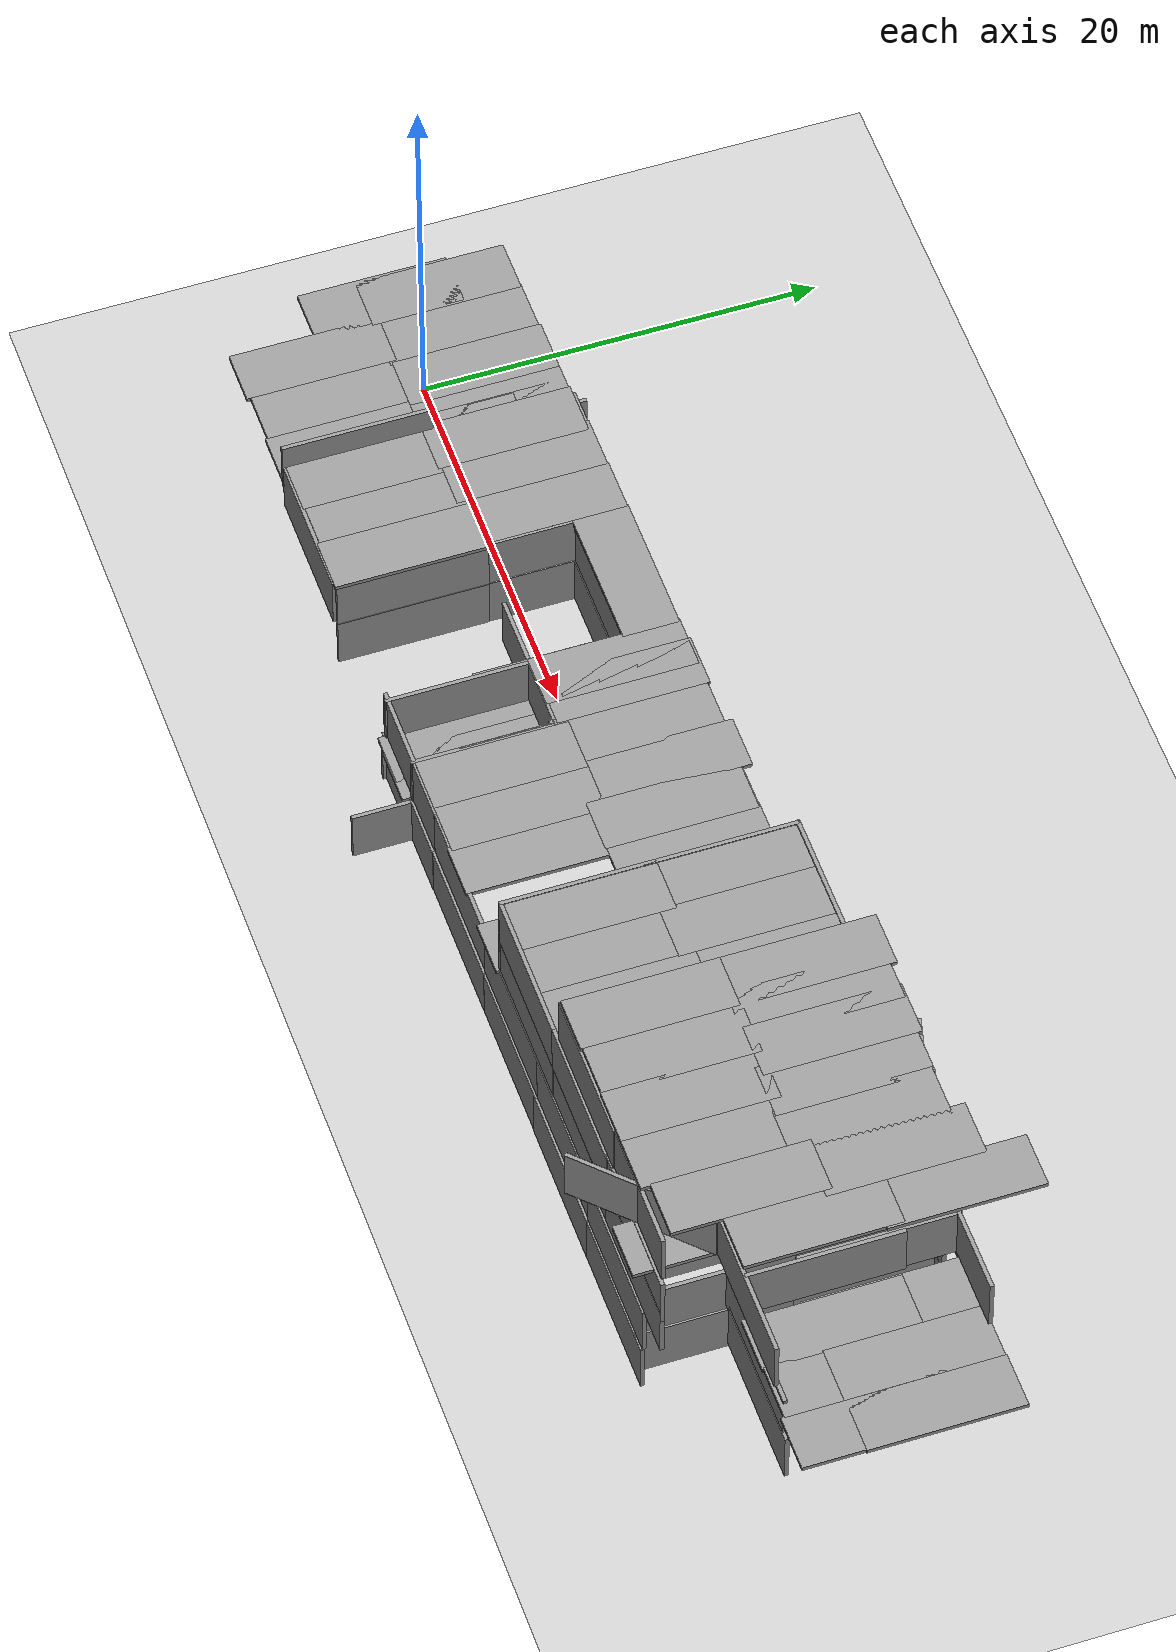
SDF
<sdf version="1.6">
 <world name="default">
  <physics name="default_physics" default="0" type="ode">
   <ode>
    <solver>
     <type>quick</type>
     <iters>100</iters>
     <sor>1</sor>
     <use_dynamic_moi_rescaling>0</use_dynamic_moi_rescaling>
    </solver>
    <constraints>
     <cfm>0</cfm>
     <erp>0.2</erp>
     <contact_max_correcting_vel>0.1</contact_max_correcting_vel>
     <contact_surface_layer>0</contact_surface_layer>
    </constraints>
   </ode>
   <real_time_update_rate>-1</real_time_update_rate>
   <max_step_size>0.001</max_step_size>
   <real_time_factor>1</real_time_factor>
  </physics>
  <gravity>0 0 -9.8</gravity>
  <light name="sun" type="directional">
   <pose>0 0 10 0 -0 0</pose>
   <diffuse>0.8 0.8 0.8 1</diffuse>
   <specular>0.2 0.2 0.2 1</specular>
   <attenuation>
    <range>1000</range>
    <constant>0.9</constant>
    <linear>0.01</linear>
    <quadratic>0.001</quadratic>
   </attenuation>
   <direction>-0.5 0.1 -0.9</direction>
  </light>
  <model name="ground_plane">
   <static>1</static>
   <link name="link">
    <collision name="collision">
     <geometry><plane><normal>0 0 1</normal><size>5000 5000</size></plane></geometry>
     <surface><friction><ode><mu>100</mu><mu2>50</mu2></ode></friction></surface>
    </collision>
    <visual name="runway">
     <pose>0 0 0.005 0 -0 0</pose>
     <cast_shadows>0</cast_shadows>
     <geometry><plane><normal>0 0 1</normal><size>1829 45</size></plane></geometry>
     <material>
      <script><uri>file://media/materials/scripts/gazebo.material</uri><name>Gazebo/Runway</name></script>
     </material>
    </visual>
    <visual name="grass">
     <pose>0 0 -0.1 0 -0 0</pose>
     <cast_shadows>0</cast_shadows>
     <geometry><plane><normal>0 0 1</normal><size>5000 5000</size></plane></geometry>
     <material>
      <script><uri>file://media/materials/scripts/gazebo.material</uri><name>Gazebo/Grass</name></script>
     </material>
    </visual>
   </link>
  </model>
  <magnetic_field>6e-06 2.3e-05 -4.2e-05</magnetic_field>
  <atmosphere type="adiabatic"/>
  <scene><ambient>0.4 0.4 0.4 1</ambient><background>0.7 0.7 0.7 1</background><shadows>1</shadows></scene>
  <spherical_coordinates>
   <surface_model>EARTH_WGS84</surface_model>
   <latitude_deg>0</latitude_deg>
   <longitude_deg>0</longitude_deg>
   <elevation>0</elevation>
   <heading_deg>0</heading_deg>
  </spherical_coordinates>
  <model name="grey_wall_0_clone">
   <static>1</static>
   <link name="link">
    <pose>0 0 1.4 0 -0 0</pose>
    <collision name="collision"><geometry><box><size>7.5 0.2 2.8</size></box></geometry></collision>
    <visual name="visual">
     <cast_shadows>0</cast_shadows>
     <geometry><box><size>7.5 0.2 2.8</size></box></geometry>
     <material>
      <script>
       <uri>model://grey_wall/materials/scripts</uri>
       <uri>model://grey_wall/materials/textures</uri>
       <name>vrc/grey_wall</name>
      </script>
     </material>
    </visual>
   </link>
   <pose>10.7245 5.24992 0 0 -0 0</pose>
  </model>
  <model name="grey_wall_0_clone_0">
   <static>1</static>
   <link name="link">
    <pose>0 0 1.4 0 -0 0</pose>
    <collision name="collision"><geometry><box><size>7.5 0.2 2.8</size></box></geometry></collision>
    <visual name="visual">
     <cast_shadows>0</cast_shadows>
     <geometry><box><size>7.5 0.2 2.8</size></box></geometry>
     <material>
      <script>
       <uri>model://grey_wall/materials/scripts</uri>
       <uri>model://grey_wall/materials/textures</uri>
       <name>vrc/grey_wall</name>
      </script>
     </material>
    </visual>
   </link>
   <pose>18.1379 5.35276 0 0 -0 0</pose>
  </model>
  <model name="grey_wall_0_clone_1">
   <static>1</static>
   <link name="link">
    <pose>0 0 1.4 0 -0 0</pose>
    <collision name="collision"><geometry><box><size>7.5 0.2 2.8</size></box></geometry></collision>
    <visual name="visual">
     <cast_shadows>0</cast_shadows>
     <geometry><box><size>7.5 0.2 2.8</size></box></geometry>
     <material>
      <script>
       <uri>model://grey_wall/materials/scripts</uri>
       <uri>model://grey_wall/materials/textures</uri>
       <name>vrc/grey_wall</name>
      </script>
     </material>
    </visual>
   </link>
   <pose>25.5945 5.27252 0 0 -0 0</pose>
  </model>
  <model name="grey_wall_0_clone_2">
   <static>1</static>
   <link name="link">
    <pose>0 0 1.4 0 -0 0</pose>
    <collision name="collision"><geometry><box><size>7.5 0.2 2.8</size></box></geometry></collision>
    <visual name="visual">
     <cast_shadows>0</cast_shadows>
     <geometry><box><size>7.5 0.2 2.8</size></box></geometry>
     <material>
      <script>
       <uri>model://grey_wall/materials/scripts</uri>
       <uri>model://grey_wall/materials/textures</uri>
       <name>vrc/grey_wall</name>
      </script>
     </material>
    </visual>
   </link>
   <pose>32.8671 5.27341 0 0 -0 0</pose>
  </model>
  <model name="grey_wall_0_clone_3">
   <static>1</static>
   <link name="link">
    <pose>0 0 1.4 0 -0 0</pose>
    <collision name="collision"><geometry><box><size>7.5 0.2 2.8</size></box></geometry></collision>
    <visual name="visual">
     <cast_shadows>0</cast_shadows>
     <geometry><box><size>7.5 0.2 2.8</size></box></geometry>
     <material>
      <script>
       <uri>model://grey_wall/materials/scripts</uri>
       <uri>model://grey_wall/materials/textures</uri>
       <name>vrc/grey_wall</name>
      </script>
     </material>
    </visual>
   </link>
   <pose>40.2229 5.26287 0 0 -0 0</pose>
  </model>
  <model name="grey_wall_0_clone_4">
   <static>1</static>
   <link name="link">
    <pose>0 0 1.4 0 -0 0</pose>
    <collision name="collision"><geometry><box><size>7.5 0.2 2.8</size></box></geometry></collision>
    <visual name="visual">
     <cast_shadows>0</cast_shadows>
     <geometry><box><size>7.5 0.2 2.8</size></box></geometry>
     <material>
      <script>
       <uri>model://grey_wall/materials/scripts</uri>
       <uri>model://grey_wall/materials/textures</uri>
       <name>vrc/grey_wall</name>
      </script>
     </material>
    </visual>
   </link>
   <pose>47.6141 5.23314 0 0 -0 0</pose>
  </model>
  <model name="grey_wall_0_clone_5">
   <static>1</static>
   <link name="link">
    <pose>0 0 1.4 0 -0 0</pose>
    <collision name="collision"><geometry><box><size>7.5 0.2 2.8</size></box></geometry></collision>
    <visual name="visual">
     <cast_shadows>0</cast_shadows>
     <geometry><box><size>7.5 0.2 2.8</size></box></geometry>
     <material>
      <script>
       <uri>model://grey_wall/materials/scripts</uri>
       <uri>model://grey_wall/materials/textures</uri>
       <name>vrc/grey_wall</name>
      </script>
     </material>
    </visual>
   </link>
   <pose>25.0989 -8.97825 0 0 -0 0</pose>
  </model>
  <model name="grey_wall_0_clone_6">
   <static>1</static>
   <link name="link">
    <pose>0 0 1.4 0 -0 0</pose>
    <collision name="collision"><geometry><box><size>7.5 0.2 2.8</size></box></geometry></collision>
    <visual name="visual">
     <cast_shadows>0</cast_shadows>
     <geometry><box><size>7.5 0.2 2.8</size></box></geometry>
     <material>
      <script>
       <uri>model://grey_wall/materials/scripts</uri>
       <uri>model://grey_wall/materials/textures</uri>
       <name>vrc/grey_wall</name>
      </script>
     </material>
    </visual>
   </link>
   <pose>32.5083 -8.96234 0 0 -0 0</pose>
  </model>
  <model name="grey_wall_0_clone_7">
   <static>1</static>
   <link name="link">
    <pose>0 0 1.4 0 -0 0</pose>
    <collision name="collision"><geometry><box><size>7.5 0.2 2.8</size></box></geometry></collision>
    <visual name="visual">
     <cast_shadows>0</cast_shadows>
     <geometry><box><size>7.5 0.2 2.8</size></box></geometry>
     <material>
      <script>
       <uri>model://grey_wall/materials/scripts</uri>
       <uri>model://grey_wall/materials/textures</uri>
       <name>vrc/grey_wall</name>
      </script>
     </material>
    </visual>
   </link>
   <pose>39.9344 -8.95946 0 0 -0 0</pose>
  </model>
  <model name="grey_wall_0_clone_8">
   <static>1</static>
   <link name="link">
    <pose>0 0 1.4 0 -0 0</pose>
    <collision name="collision"><geometry><box><size>7.5 0.2 2.8</size></box></geometry></collision>
    <visual name="visual">
     <cast_shadows>0</cast_shadows>
     <geometry><box><size>7.5 0.2 2.8</size></box></geometry>
     <material>
      <script>
       <uri>model://grey_wall/materials/scripts</uri>
       <uri>model://grey_wall/materials/textures</uri>
       <name>vrc/grey_wall</name>
      </script>
     </material>
    </visual>
   </link>
   <pose>47.1692 -8.98031 0 0 -0 0</pose>
  </model>
  <model name="grey_wall_0_clone_8_clone">
   <static>1</static>
   <link name="link">
    <pose>0 0 1.4 0 -0 0</pose>
    <collision name="collision"><geometry><box><size>7.5 0.2 2.8</size></box></geometry></collision>
    <visual name="visual">
     <cast_shadows>0</cast_shadows>
     <geometry><box><size>7.5 0.2 2.8</size></box></geometry>
     <material>
      <script>
       <uri>model://grey_wall/materials/scripts</uri>
       <uri>model://grey_wall/materials/textures</uri>
       <name>vrc/grey_wall</name>
      </script>
     </material>
    </visual>
   </link>
   <pose>54.6088 -8.97122 0 0 -0 0</pose>
  </model>
  <model name="grey_wall_0_clone_10">
   <static>1</static>
   <link name="link">
    <pose>0 0 1.4 0 -0 0</pose>
    <collision name="collision"><geometry><box><size>7.5 0.2 2.8</size></box></geometry></collision>
    <visual name="visual">
     <cast_shadows>0</cast_shadows>
     <geometry><box><size>7.5 0.2 2.8</size></box></geometry>
     <material>
      <script>
       <uri>model://grey_wall/materials/scripts</uri>
       <uri>model://grey_wall/materials/textures</uri>
       <name>vrc/grey_wall</name>
      </script>
     </material>
    </visual>
   </link>
   <pose>25.0498 -8.85326 2.83061 0 -0 0</pose>
  </model>
  <model name="grey_wall_0_clone_10_clone">
   <static>1</static>
   <link name="link">
    <pose>0 0 1.4 0 -0 0</pose>
    <collision name="collision"><geometry><box><size>7.5 0.2 2.8</size></box></geometry></collision>
    <visual name="visual">
     <cast_shadows>0</cast_shadows>
     <geometry><box><size>7.5 0.2 2.8</size></box></geometry>
     <material>
      <script>
       <uri>model://grey_wall/materials/scripts</uri>
       <uri>model://grey_wall/materials/textures</uri>
       <name>vrc/grey_wall</name>
      </script>
     </material>
    </visual>
   </link>
   <pose>32.4685 -8.83738 2.83061 0 -0 0</pose>
  </model>
  <model name="grey_wall_0_clone_10_clone_clone">
   <static>1</static>
   <link name="link">
    <pose>0 0 1.4 0 -0 0</pose>
    <collision name="collision"><geometry><box><size>7.5 0.2 2.8</size></box></geometry></collision>
    <visual name="visual">
     <cast_shadows>0</cast_shadows>
     <geometry><box><size>7.5 0.2 2.8</size></box></geometry>
     <material>
      <script>
       <uri>model://grey_wall/materials/scripts</uri>
       <uri>model://grey_wall/materials/textures</uri>
       <name>vrc/grey_wall</name>
      </script>
     </material>
    </visual>
   </link>
   <pose>39.8658 -8.86209 2.83061 0 -0 0</pose>
  </model>
  <model name="grey_wall_0_clone_10_clone_clone_0">
   <static>1</static>
   <link name="link">
    <pose>0 0 1.4 0 -0 0</pose>
    <collision name="collision"><geometry><box><size>7.5 0.2 2.8</size></box></geometry></collision>
    <visual name="visual">
     <cast_shadows>0</cast_shadows>
     <geometry><box><size>7.5 0.2 2.8</size></box></geometry>
     <material>
      <script>
       <uri>model://grey_wall/materials/scripts</uri>
       <uri>model://grey_wall/materials/textures</uri>
       <name>vrc/grey_wall</name>
      </script>
     </material>
    </visual>
   </link>
   <pose>47.2025 -8.86122 2.83061 0 -0 0</pose>
  </model>
  <model name="grey_wall_0_clone_10_clone_clone_1">
   <static>1</static>
   <link name="link">
    <pose>0 0 1.4 0 -0 0</pose>
    <collision name="collision"><geometry><box><size>7.5 0.2 2.8</size></box></geometry></collision>
    <visual name="visual">
     <cast_shadows>0</cast_shadows>
     <geometry><box><size>7.5 0.2 2.8</size></box></geometry>
     <material>
      <script>
       <uri>model://grey_wall/materials/scripts</uri>
       <uri>model://grey_wall/materials/textures</uri>
       <name>vrc/grey_wall</name>
      </script>
     </material>
    </visual>
   </link>
   <pose>54.6088 -8.89277 2.83061 0 -0 0</pose>
  </model>
  <model name="grey_wall_0_clone_10_clone_clone_2">
   <static>1</static>
   <link name="link">
    <pose>0 0 1.4 0 -0 0</pose>
    <collision name="collision"><geometry><box><size>7.5 0.2 2.8</size></box></geometry></collision>
    <visual name="visual">
     <cast_shadows>0</cast_shadows>
     <geometry><box><size>7.5 0.2 2.8</size></box></geometry>
     <material>
      <script>
       <uri>model://grey_wall/materials/scripts</uri>
       <uri>model://grey_wall/materials/textures</uri>
       <name>vrc/grey_wall</name>
      </script>
     </material>
    </visual>
   </link>
   <pose>10.6982 5.25569 2.83061 0 -0 0</pose>
  </model>
  <model name="grey_wall_0_clone_10_clone_clone_3">
   <static>1</static>
   <link name="link">
    <pose>0 0 1.4 0 -0 0</pose>
    <collision name="collision"><geometry><box><size>7.5 0.2 2.8</size></box></geometry></collision>
    <visual name="visual">
     <cast_shadows>0</cast_shadows>
     <geometry><box><size>7.5 0.2 2.8</size></box></geometry>
     <material>
      <script>
       <uri>model://grey_wall/materials/scripts</uri>
       <uri>model://grey_wall/materials/textures</uri>
       <name>vrc/grey_wall</name>
      </script>
     </material>
    </visual>
   </link>
   <pose>17.8888 5.34719 2.83061 0 -0 0</pose>
  </model>
  <model name="grey_wall_0_clone_10_clone_clone_4">
   <static>1</static>
   <link name="link">
    <pose>0 0 1.4 0 -0 0</pose>
    <collision name="collision"><geometry><box><size>7.5 0.2 2.8</size></box></geometry></collision>
    <visual name="visual">
     <cast_shadows>0</cast_shadows>
     <geometry><box><size>7.5 0.2 2.8</size></box></geometry>
     <material>
      <script>
       <uri>model://grey_wall/materials/scripts</uri>
       <uri>model://grey_wall/materials/textures</uri>
       <name>vrc/grey_wall</name>
      </script>
     </material>
    </visual>
   </link>
   <pose>25.311 5.32515 2.83061 0 -0 0</pose>
  </model>
  <model name="grey_wall_0_clone_10_clone_clone_5">
   <static>1</static>
   <link name="link">
    <pose>0 0 1.4 0 -0 0</pose>
    <collision name="collision"><geometry><box><size>7.5 0.2 2.8</size></box></geometry></collision>
    <visual name="visual">
     <cast_shadows>0</cast_shadows>
     <geometry><box><size>7.5 0.2 2.8</size></box></geometry>
     <material>
      <script>
       <uri>model://grey_wall/materials/scripts</uri>
       <uri>model://grey_wall/materials/textures</uri>
       <name>vrc/grey_wall</name>
      </script>
     </material>
    </visual>
   </link>
   <pose>32.6267 5.3026 2.83061 0 -0 0</pose>
  </model>
  <model name="grey_wall_0_clone_10_clone_clone_6">
   <static>1</static>
   <link name="link">
    <pose>0 0 1.4 0 -0 0</pose>
    <collision name="collision"><geometry><box><size>7.5 0.2 2.8</size></box></geometry></collision>
    <visual name="visual">
     <cast_shadows>0</cast_shadows>
     <geometry><box><size>7.5 0.2 2.8</size></box></geometry>
     <material>
      <script>
       <uri>model://grey_wall/materials/scripts</uri>
       <uri>model://grey_wall/materials/textures</uri>
       <name>vrc/grey_wall</name>
      </script>
     </material>
    </visual>
   </link>
   <pose>40.0722 5.27757 2.83061 0 -0 0</pose>
  </model>
  <model name="grey_wall_0_clone_10_clone_clone_7">
   <static>1</static>
   <link name="link">
    <pose>0 0 1.4 0 -0 0</pose>
    <collision name="collision"><geometry><box><size>7.5 0.2 2.8</size></box></geometry></collision>
    <visual name="visual">
     <cast_shadows>0</cast_shadows>
     <geometry><box><size>7.5 0.2 2.8</size></box></geometry>
     <material>
      <script>
       <uri>model://grey_wall/materials/scripts</uri>
       <uri>model://grey_wall/materials/textures</uri>
       <name>vrc/grey_wall</name>
      </script>
     </material>
    </visual>
   </link>
   <pose>47.3454 5.26753 2.83061 0 -0 0</pose>
  </model>
  <model name="grey_wall_0_clone_1_clone">
   <static>1</static>
   <link name="link">
    <pose>0 0 1.4 0 -0 0</pose>
    <collision name="collision"><geometry><box><size>7.5 0.2 2.8</size></box></geometry></collision>
    <visual name="visual">
     <cast_shadows>0</cast_shadows>
     <geometry><box><size>7.5 0.2 2.8</size></box></geometry>
     <material>
      <script>
       <uri>model://grey_wall/materials/scripts</uri>
       <uri>model://grey_wall/materials/textures</uri>
       <name>vrc/grey_wall</name>
      </script>
     </material>
    </visual>
   </link>
   <pose>14.4589 -5.28722 0 0 0 -1.5708</pose>
  </model>
  <model name="grey_wall_0_clone_10_clone_clone_3_clone">
   <static>1</static>
   <link name="link">
    <pose>0 0 1.4 0 -0 0</pose>
    <collision name="collision"><geometry><box><size>7.5 0.2 2.8</size></box></geometry></collision>
    <visual name="visual">
     <cast_shadows>0</cast_shadows>
     <geometry><box><size>7.5 0.2 2.8</size></box></geometry>
     <material>
      <script>
       <uri>model://grey_wall/materials/scripts</uri>
       <uri>model://grey_wall/materials/textures</uri>
       <name>vrc/grey_wall</name>
      </script>
     </material>
    </visual>
   </link>
   <pose>14.433 -5.27177 2.83061 0 0 -1.5708</pose>
  </model>
  <model name="grey_wall_0_clone_1_clone_clone">
   <static>1</static>
   <link name="link">
    <pose>0 0 1.4 0 -0 0</pose>
    <collision name="collision"><geometry><box><size>7.5 0.2 2.8</size></box></geometry></collision>
    <visual name="visual">
     <cast_shadows>0</cast_shadows>
     <geometry><box><size>7.5 0.2 2.8</size></box></geometry>
     <material>
      <script>
       <uri>model://grey_wall/materials/scripts</uri>
       <uri>model://grey_wall/materials/textures</uri>
       <name>vrc/grey_wall</name>
      </script>
     </material>
    </visual>
   </link>
   <pose>14.4307 1.60378 0 0 0 -1.5708</pose>
  </model>
  <model name="grey_wall_0_clone_10_clone_clone_3_clone_clone">
   <static>1</static>
   <link name="link">
    <pose>0 0 1.4 0 -0 0</pose>
    <collision name="collision"><geometry><box><size>7.5 0.2 2.8</size></box></geometry></collision>
    <visual name="visual">
     <cast_shadows>0</cast_shadows>
     <geometry><box><size>7.5 0.2 2.8</size></box></geometry>
     <material>
      <script>
       <uri>model://grey_wall/materials/scripts</uri>
       <uri>model://grey_wall/materials/textures</uri>
       <name>vrc/grey_wall</name>
      </script>
     </material>
    </visual>
   </link>
   <pose>14.3909 -0.780595 2.83061 0 0 -1.5708</pose>
  </model>
  <model name="grey_wall_0_clone_10_clone_clone_3_clone_0">
   <static>1</static>
   <link name="link">
    <pose>0 0 1.4 0 -0 0</pose>
    <collision name="collision"><geometry><box><size>7.5 0.2 2.8</size></box></geometry></collision>
    <visual name="visual">
     <cast_shadows>0</cast_shadows>
     <geometry><box><size>7.5 0.2 2.8</size></box></geometry>
     <material>
      <script>
       <uri>model://grey_wall/materials/scripts</uri>
       <uri>model://grey_wall/materials/textures</uri>
       <name>vrc/grey_wall</name>
      </script>
     </material>
    </visual>
   </link>
   <pose>18.0863 2.86625 2.83061 0 -0 0</pose>
  </model>
  <model name="grey_wall_0_clone_0_clone">
   <static>1</static>
   <link name="link">
    <pose>0 0 1.4 0 -0 0</pose>
    <collision name="collision"><geometry><box><size>7.5 0.2 2.8</size></box></geometry></collision>
    <visual name="visual">
     <cast_shadows>0</cast_shadows>
     <geometry><box><size>7.5 0.2 2.8</size></box></geometry>
     <material>
      <script>
       <uri>model://grey_wall/materials/scripts</uri>
       <uri>model://grey_wall/materials/textures</uri>
       <name>vrc/grey_wall</name>
      </script>
     </material>
    </visual>
   </link>
   <pose>18.1341 2.8231 0 0 -0 0</pose>
  </model>
  <model name="grey_wall_0_clone_10_clone_clone_3_clone_clone_clone">
   <static>1</static>
   <link name="link">
    <pose>0 0 1.4 0 -0 0</pose>
    <collision name="collision"><geometry><box><size>7.5 0.2 2.8</size></box></geometry></collision>
    <visual name="visual">
     <cast_shadows>0</cast_shadows>
     <geometry><box><size>7.5 0.2 2.8</size></box></geometry>
     <material>
      <script>
       <uri>model://grey_wall/materials/scripts</uri>
       <uri>model://grey_wall/materials/textures</uri>
       <name>vrc/grey_wall</name>
      </script>
     </material>
    </visual>
   </link>
   <pose>25.4024 1.55722 2.83061 0 0 -1.5708</pose>
  </model>
  <model name="grey_wall_0_clone_10_clone_clone_3_clone_clone_clone_0">
   <static>1</static>
   <link name="link">
    <pose>0 0 1.4 0 -0 0</pose>
    <collision name="collision"><geometry><box><size>7.5 0.2 2.8</size></box></geometry></collision>
    <visual name="visual">
     <cast_shadows>0</cast_shadows>
     <geometry><box><size>7.5 0.2 2.8</size></box></geometry>
     <material>
      <script>
       <uri>model://grey_wall/materials/scripts</uri>
       <uri>model://grey_wall/materials/textures</uri>
       <name>vrc/grey_wall</name>
      </script>
     </material>
    </visual>
   </link>
   <pose>25.5803 -2.87326 2.83061 0 0 -1.5708</pose>
  </model>
  <model name="grey_wall_0_clone_1_clone_clone_0">
   <static>1</static>
   <link name="link">
    <pose>0 0 1.4 0 -0 0</pose>
    <collision name="collision"><geometry><box><size>7.5 0.2 2.8</size></box></geometry></collision>
    <visual name="visual">
     <cast_shadows>0</cast_shadows>
     <geometry><box><size>7.5 0.2 2.8</size></box></geometry>
     <material>
      <script>
       <uri>model://grey_wall/materials/scripts</uri>
       <uri>model://grey_wall/materials/textures</uri>
       <name>vrc/grey_wall</name>
      </script>
     </material>
    </visual>
   </link>
   <pose>21.772 -0.922629 0 0 0 -1.5708</pose>
  </model>
  <model name="grey_wall_0_clone_1_clone_clone_1">
   <static>1</static>
   <link name="link">
    <pose>0 0 1.4 0 -0 0</pose>
    <collision name="collision"><geometry><box><size>7.5 0.2 2.8</size></box></geometry></collision>
    <visual name="visual">
     <cast_shadows>0</cast_shadows>
     <geometry><box><size>7.5 0.2 2.8</size></box></geometry>
     <material>
      <script>
       <uri>model://grey_wall/materials/scripts</uri>
       <uri>model://grey_wall/materials/textures</uri>
       <name>vrc/grey_wall</name>
      </script>
     </material>
    </visual>
   </link>
   <pose>21.8008 -5.49226 0 0 0 -1.5708</pose>
  </model>
  <model name="grey_wall_0_clone_10_clone_clone_3_clone_clone_clone_clone">
   <static>1</static>
   <link name="link">
    <pose>0 0 1.4 0 -0 0</pose>
    <collision name="collision"><geometry><box><size>7.5 0.2 2.8</size></box></geometry></collision>
    <visual name="visual">
     <cast_shadows>0</cast_shadows>
     <geometry><box><size>7.5 0.2 2.8</size></box></geometry>
     <material>
      <script>
       <uri>model://grey_wall/materials/scripts</uri>
       <uri>model://grey_wall/materials/textures</uri>
       <name>vrc/grey_wall</name>
      </script>
     </material>
    </visual>
   </link>
   <pose>21.6407 -0.916233 2.83061 0 0 -1.5708</pose>
  </model>
  <model name="grey_wall_0_clone_10_clone_clone_3_clone_clone_clone_clone_0">
   <static>1</static>
   <link name="link">
    <pose>0 0 1.4 0 -0 0</pose>
    <collision name="collision"><geometry><box><size>7.5 0.2 2.8</size></box></geometry></collision>
    <visual name="visual">
     <cast_shadows>0</cast_shadows>
     <geometry><box><size>7.5 0.2 2.8</size></box></geometry>
     <material>
      <script>
       <uri>model://grey_wall/materials/scripts</uri>
       <uri>model://grey_wall/materials/textures</uri>
       <name>vrc/grey_wall</name>
      </script>
     </material>
    </visual>
   </link>
   <pose>21.7402 -5.27279 2.83061 0 0 -1.5708</pose>
  </model>
  <model name="grey_wall_0_clone_1_clone_clone_0_clone">
   <static>1</static>
   <link name="link">
    <pose>0 0 1.4 0 -0 0</pose>
    <collision name="collision"><geometry><box><size>7.5 0.2 2.8</size></box></geometry></collision>
    <visual name="visual">
     <cast_shadows>0</cast_shadows>
     <geometry><box><size>7.5 0.2 2.8</size></box></geometry>
     <material>
      <script>
       <uri>model://grey_wall/materials/scripts</uri>
       <uri>model://grey_wall/materials/textures</uri>
       <name>vrc/grey_wall</name>
      </script>
     </material>
    </visual>
   </link>
   <pose>25.414 1.65261 0 0 0 -1.5708</pose>
  </model>
  <model name="grey_wall_0_clone_1_clone_clone_0_clone_0">
   <static>1</static>
   <link name="link">
    <pose>0 0 1.4 0 -0 0</pose>
    <collision name="collision"><geometry><box><size>7.5 0.2 2.8</size></box></geometry></collision>
    <visual name="visual">
     <cast_shadows>0</cast_shadows>
     <geometry><box><size>7.5 0.2 2.8</size></box></geometry>
     <material>
      <script>
       <uri>model://grey_wall/materials/scripts</uri>
       <uri>model://grey_wall/materials/textures</uri>
       <name>vrc/grey_wall</name>
      </script>
     </material>
    </visual>
   </link>
   <pose>25.6372 -8.21965 0 0 0 -1.5708</pose>
  </model>
  <model name="grey_wall_0_clone_10_clone_clone_3_clone_clone_clone_0_clone">
   <static>1</static>
   <link name="link">
    <pose>0 0 1.4 0 -0 0</pose>
    <collision name="collision"><geometry><box><size>7.5 0.2 2.8</size></box></geometry></collision>
    <visual name="visual">
     <cast_shadows>0</cast_shadows>
     <geometry><box><size>7.5 0.2 2.8</size></box></geometry>
     <material>
      <script>
       <uri>model://grey_wall/materials/scripts</uri>
       <uri>model://grey_wall/materials/textures</uri>
       <name>vrc/grey_wall</name>
      </script>
     </material>
    </visual>
   </link>
   <pose>25.562 -5.25695 2.83061 0 0 -1.5708</pose>
  </model>
  <model name="grey_wall_0_clone_10_clone_0">
   <static>1</static>
   <link name="link">
    <pose>0 0 1.4 0 -0 0</pose>
    <collision name="collision"><geometry><box><size>7.5 0.2 2.8</size></box></geometry></collision>
    <visual name="visual">
     <cast_shadows>0</cast_shadows>
     <geometry><box><size>7.5 0.2 2.8</size></box></geometry>
     <material>
      <script>
       <uri>model://grey_wall/materials/scripts</uri>
       <uri>model://grey_wall/materials/textures</uri>
       <name>vrc/grey_wall</name>
      </script>
     </material>
    </visual>
   </link>
   <pose>21.7238 -1.91976 2.83061 0 -0 0</pose>
  </model>
  <model name="grey_wall_0_clone_10_clone_0_clone">
   <static>1</static>
   <link name="link">
    <pose>0 0 1.4 0 -0 0</pose>
    <collision name="collision"><geometry><box><size>7.5 0.2 2.8</size></box></geometry></collision>
    <visual name="visual">
     <cast_shadows>0</cast_shadows>
     <geometry><box><size>7.5 0.2 2.8</size></box></geometry>
     <material>
      <script>
       <uri>model://grey_wall/materials/scripts</uri>
       <uri>model://grey_wall/materials/textures</uri>
       <name>vrc/grey_wall</name>
      </script>
     </material>
    </visual>
   </link>
   <pose>25.5163 -5.684 2.83061 1.5708 0 -1.5708</pose>
  </model>
  <model name="grey_wall_0_clone_10_clone_0_clone_clone">
   <static>1</static>
   <link name="link">
    <pose>0 0 1.4 0 -0 0</pose>
    <collision name="collision"><geometry><box><size>7.5 0.2 2.8</size></box></geometry></collision>
    <visual name="visual">
     <cast_shadows>0</cast_shadows>
     <geometry><box><size>7.5 0.2 2.8</size></box></geometry>
     <material>
      <script>
       <uri>model://grey_wall/materials/scripts</uri>
       <uri>model://grey_wall/materials/textures</uri>
       <name>vrc/grey_wall</name>
      </script>
     </material>
    </visual>
   </link>
   <pose>24.4817 -5.63211 2.8306 1.5708 0 -1.5708</pose>
  </model>
  <model name="grey_wall_0_clone_10_clone_0_clone_clone_clone">
   <static>1</static>
   <link name="link">
    <pose>0 0 1.4 0 -0 0</pose>
    <collision name="collision"><geometry><box><size>7.5 0.2 2.8</size></box></geometry></collision>
    <visual name="visual">
     <cast_shadows>0</cast_shadows>
     <geometry><box><size>7.5 0.2 2.8</size></box></geometry>
     <material>
      <script>
       <uri>model://grey_wall/materials/scripts</uri>
       <uri>model://grey_wall/materials/textures</uri>
       <name>vrc/grey_wall</name>
      </script>
     </material>
    </visual>
   </link>
   <pose>25.5834 1.89085 5.5331 1.5708 0 -1.5708</pose>
  </model>
  <model name="grey_wall_0_clone_10_clone_0_clone_clone_clone_clone">
   <static>1</static>
   <link name="link">
    <pose>0 0 1.4 0 -0 0</pose>
    <collision name="collision"><geometry><box><size>7.5 0.2 2.8</size></box></geometry></collision>
    <visual name="visual">
     <cast_shadows>0</cast_shadows>
     <geometry><box><size>7.5 0.2 2.8</size></box></geometry>
     <material>
      <script>
       <uri>model://grey_wall/materials/scripts</uri>
       <uri>model://grey_wall/materials/textures</uri>
       <name>vrc/grey_wall</name>
      </script>
     </material>
    </visual>
   </link>
   <pose>24.3486 1.77269 5.5331 1.5708 0 -1.5708</pose>
  </model>
  <model name="grey_wall_0_clone_10_clone_0_clone_clone_clone_clone_0">
   <static>1</static>
   <link name="link">
    <pose>0 0 1.4 0 -0 0</pose>
    <collision name="collision"><geometry><box><size>7.5 0.2 2.8</size></box></geometry></collision>
    <visual name="visual">
     <cast_shadows>0</cast_shadows>
     <geometry><box><size>7.5 0.2 2.8</size></box></geometry>
     <material>
      <script>
       <uri>model://grey_wall/materials/scripts</uri>
       <uri>model://grey_wall/materials/textures</uri>
       <name>vrc/grey_wall</name>
      </script>
     </material>
    </visual>
   </link>
   <pose>17.9707 2.68641 5.53311 1.5708 4e-06 3.14159</pose>
  </model>
  <model name="grey_wall_0_clone_10_clone_0_clone_clone_clone_clone_1">
   <static>1</static>
   <link name="link">
    <pose>0 0 1.4 0 -0 0</pose>
    <collision name="collision"><geometry><box><size>7.5 0.2 2.8</size></box></geometry></collision>
    <visual name="visual">
     <cast_shadows>0</cast_shadows>
     <geometry><box><size>7.5 0.2 2.8</size></box></geometry>
     <material>
      <script>
       <uri>model://grey_wall/materials/scripts</uri>
       <uri>model://grey_wall/materials/textures</uri>
       <name>vrc/grey_wall</name>
      </script>
     </material>
    </visual>
   </link>
   <pose>11.5899 1.64731 5.5331 1.5708 0 -1.5708</pose>
  </model>
  <model name="grey_wall_0_clone_10_clone_0_clone_clone_clone_clone_2">
   <static>1</static>
   <link name="link">
    <pose>0 0 1.4 0 -0 0</pose>
    <collision name="collision"><geometry><box><size>7.5 0.2 2.8</size></box></geometry></collision>
    <visual name="visual">
     <cast_shadows>0</cast_shadows>
     <geometry><box><size>7.5 0.2 2.8</size></box></geometry>
     <material>
      <script>
       <uri>model://grey_wall/materials/scripts</uri>
       <uri>model://grey_wall/materials/textures</uri>
       <name>vrc/grey_wall</name>
      </script>
     </material>
    </visual>
   </link>
   <pose>9.32002 1.47707 5.5331 1.5708 0 -1.5708</pose>
  </model>
  <model name="grey_wall_0_clone_10_clone_0_clone_clone_clone_clone_3">
   <static>1</static>
   <link name="link">
    <pose>0 0 1.4 0 -0 0</pose>
    <collision name="collision"><geometry><box><size>7.5 0.2 2.8</size></box></geometry></collision>
    <visual name="visual">
     <cast_shadows>0</cast_shadows>
     <geometry><box><size>7.5 0.2 2.8</size></box></geometry>
     <material>
      <script>
       <uri>model://grey_wall/materials/scripts</uri>
       <uri>model://grey_wall/materials/textures</uri>
       <name>vrc/grey_wall</name>
      </script>
     </material>
    </visual>
   </link>
   <pose>14.3486 1.6947 5.5331 1.5708 0 -1.5708</pose>
  </model>
  <model name="grey_wall_0_clone_10_clone_0_clone_clone_clone_clone_4">
   <static>1</static>
   <link name="link">
    <pose>0 0 1.4 0 -0 0</pose>
    <collision name="collision"><geometry><box><size>7.5 0.2 2.8</size></box></geometry></collision>
    <visual name="visual">
     <cast_shadows>0</cast_shadows>
     <geometry><box><size>7.5 0.2 2.8</size></box></geometry>
     <material>
      <script>
       <uri>model://grey_wall/materials/scripts</uri>
       <uri>model://grey_wall/materials/textures</uri>
       <name>vrc/grey_wall</name>
      </script>
     </material>
    </visual>
   </link>
   <pose>14.56 -5.34818 5.5331 1.5708 0 -1.5708</pose>
  </model>
  <model name="grey_wall_0_clone_10_clone_0_clone_clone_clone_clone_5">
   <static>1</static>
   <link name="link">
    <pose>0 0 1.4 0 -0 0</pose>
    <collision name="collision"><geometry><box><size>7.5 0.2 2.8</size></box></geometry></collision>
    <visual name="visual">
     <cast_shadows>0</cast_shadows>
     <geometry><box><size>7.5 0.2 2.8</size></box></geometry>
     <material>
      <script>
       <uri>model://grey_wall/materials/scripts</uri>
       <uri>model://grey_wall/materials/textures</uri>
       <name>vrc/grey_wall</name>
      </script>
     </material>
    </visual>
   </link>
   <pose>12.1439 -5.23018 5.5331 1.5708 0 -1.5708</pose>
  </model>
  <model name="grey_wall_0_clone_10_clone_0_clone_clone_clone_clone_6">
   <static>1</static>
   <link name="link">
    <pose>0 0 1.4 0 -0 0</pose>
    <collision name="collision"><geometry><box><size>7.5 0.2 2.8</size></box></geometry></collision>
    <visual name="visual">
     <cast_shadows>0</cast_shadows>
     <geometry><box><size>7.5 0.2 2.8</size></box></geometry>
     <material>
      <script>
       <uri>model://grey_wall/materials/scripts</uri>
       <uri>model://grey_wall/materials/textures</uri>
       <name>vrc/grey_wall</name>
      </script>
     </material>
    </visual>
   </link>
   <pose>9.58649 -5.31482 5.5331 1.5708 0 -1.5708</pose>
  </model>
  <model name="grey_wall_0_clone_10_clone_0_clone_clone_clone_clone_7">
   <static>1</static>
   <link name="link">
    <pose>0 0 1.4 0 -0 0</pose>
    <collision name="collision"><geometry><box><size>7.5 0.2 2.8</size></box></geometry></collision>
    <visual name="visual">
     <cast_shadows>0</cast_shadows>
     <geometry><box><size>7.5 0.2 2.8</size></box></geometry>
     <material>
      <script>
       <uri>model://grey_wall/materials/scripts</uri>
       <uri>model://grey_wall/materials/textures</uri>
       <name>vrc/grey_wall</name>
      </script>
     </material>
    </visual>
   </link>
   <pose>-1.21966 1.64207 4.18722 1.5708 0 -1.5708</pose>
  </model>
  <model name="grey_wall_0_clone_10_clone_0_clone_clone_clone_clone_7_clone">
   <static>1</static>
   <link name="link">
    <pose>0 0 1.4 0 -0 0</pose>
    <collision name="collision"><geometry><box><size>7.5 0.2 2.8</size></box></geometry></collision>
    <visual name="visual">
     <cast_shadows>0</cast_shadows>
     <geometry><box><size>7.5 0.2 2.8</size></box></geometry>
     <material>
      <script>
       <uri>model://grey_wall/materials/scripts</uri>
       <uri>model://grey_wall/materials/textures</uri>
       <name>vrc/grey_wall</name>
      </script>
     </material>
    </visual>
   </link>
   <pose>-1.33621 -1.21877 4.1872 1.5708 0 -1.5708</pose>
  </model>
  <model name="grey_wall_0_clone_10_clone_0_clone_clone_clone_clone_7_clone_0">
   <static>1</static>
   <link name="link">
    <pose>0 0 1.4 0 -0 0</pose>
    <collision name="collision"><geometry><box><size>7.5 0.2 2.8</size></box></geometry></collision>
    <visual name="visual">
     <cast_shadows>0</cast_shadows>
     <geometry><box><size>7.5 0.2 2.8</size></box></geometry>
     <material>
      <script>
       <uri>model://grey_wall/materials/scripts</uri>
       <uri>model://grey_wall/materials/textures</uri>
       <name>vrc/grey_wall</name>
      </script>
     </material>
    </visual>
   </link>
   <pose>1.46863 1.6641 4.1872 1.5708 0 -1.5708</pose>
  </model>
  <model name="grey_wall_0_clone_10_clone_0_clone_clone_clone_clone_7_clone_1">
   <static>1</static>
   <link name="link">
    <pose>0 0 1.4 0 -0 0</pose>
    <collision name="collision"><geometry><box><size>7.5 0.2 2.8</size></box></geometry></collision>
    <visual name="visual">
     <cast_shadows>0</cast_shadows>
     <geometry><box><size>7.5 0.2 2.8</size></box></geometry>
     <material>
      <script>
       <uri>model://grey_wall/materials/scripts</uri>
       <uri>model://grey_wall/materials/textures</uri>
       <name>vrc/grey_wall</name>
      </script>
     </material>
    </visual>
   </link>
   <pose>1.21163 -5.46045 4.1872 1.5708 0 -1.5708</pose>
  </model>
  <model name="grey_wall_0_clone_10_clone_0_clone_clone_clone_clone_7_clone_2">
   <static>1</static>
   <link name="link">
    <pose>0 0 1.4 0 -0 0</pose>
    <collision name="collision"><geometry><box><size>7.5 0.2 2.8</size></box></geometry></collision>
    <visual name="visual">
     <cast_shadows>0</cast_shadows>
     <geometry><box><size>7.5 0.2 2.8</size></box></geometry>
     <material>
      <script>
       <uri>model://grey_wall/materials/scripts</uri>
       <uri>model://grey_wall/materials/textures</uri>
       <name>vrc/grey_wall</name>
      </script>
     </material>
    </visual>
   </link>
   <pose>3.853 -5.27091 4.1872 1.5708 0 -1.5708</pose>
  </model>
  <model name="grey_wall_0_clone_10_clone_0_clone_clone_clone_clone_7_clone_3">
   <static>1</static>
   <link name="link">
    <pose>0 0 1.4 0 -0 0</pose>
    <collision name="collision"><geometry><box><size>7.5 0.2 2.8</size></box></geometry></collision>
    <visual name="visual">
     <cast_shadows>0</cast_shadows>
     <geometry><box><size>7.5 0.2 2.8</size></box></geometry>
     <material>
      <script>
       <uri>model://grey_wall/materials/scripts</uri>
       <uri>model://grey_wall/materials/textures</uri>
       <name>vrc/grey_wall</name>
      </script>
     </material>
    </visual>
   </link>
   <pose>6.61596 -5.38384 4.1872 1.5708 0 -1.5708</pose>
  </model>
  <model name="grey_wall_0_clone_10_clone_0_clone_clone_clone_clone_7_clone_4">
   <static>1</static>
   <link name="link">
    <pose>0 0 1.4 0 -0 0</pose>
    <collision name="collision"><geometry><box><size>7.5 0.2 2.8</size></box></geometry></collision>
    <visual name="visual">
     <cast_shadows>0</cast_shadows>
     <geometry><box><size>7.5 0.2 2.8</size></box></geometry>
     <material>
      <script>
       <uri>model://grey_wall/materials/scripts</uri>
       <uri>model://grey_wall/materials/textures</uri>
       <name>vrc/grey_wall</name>
      </script>
     </material>
    </visual>
   </link>
   <pose>4.09246 1.77025 4.1872 1.5708 0 -1.5708</pose>
  </model>
  <model name="grey_wall_0_clone_10_clone_0_clone_clone_clone_clone_7_clone_5">
   <static>1</static>
   <link name="link">
    <pose>0 0 1.4 0 -0 0</pose>
    <collision name="collision"><geometry><box><size>7.5 0.2 2.8</size></box></geometry></collision>
    <visual name="visual">
     <cast_shadows>0</cast_shadows>
     <geometry><box><size>7.5 0.2 2.8</size></box></geometry>
     <material>
      <script>
       <uri>model://grey_wall/materials/scripts</uri>
       <uri>model://grey_wall/materials/textures</uri>
       <name>vrc/grey_wall</name>
      </script>
     </material>
    </visual>
   </link>
   <pose>6.41355 1.77042 4.1872 1.5708 0 -1.5708</pose>
  </model>
  <model name="grey_wall_0_clone_10_clone_0_clone_clone_clone_clone_7_clone_6">
   <static>1</static>
   <link name="link">
    <pose>0 0 1.4 0 -0 0</pose>
    <collision name="collision"><geometry><box><size>7.5 0.2 2.8</size></box></geometry></collision>
    <visual name="visual">
     <cast_shadows>0</cast_shadows>
     <geometry><box><size>7.5 0.2 2.8</size></box></geometry>
     <material>
      <script>
       <uri>model://grey_wall/materials/scripts</uri>
       <uri>model://grey_wall/materials/textures</uri>
       <name>vrc/grey_wall</name>
      </script>
     </material>
    </visual>
   </link>
   <pose>7.69233 1.65748 4.1872 1.5708 0 -1.5708</pose>
  </model>
  <model name="grey_wall_0_clone_10_clone_0_clone_clone_clone_clone_7_clone_7">
   <static>1</static>
   <link name="link">
    <pose>0 0 1.4 0 -0 0</pose>
    <collision name="collision"><geometry><box><size>7.5 0.2 2.8</size></box></geometry></collision>
    <visual name="visual">
     <cast_shadows>0</cast_shadows>
     <geometry><box><size>7.5 0.2 2.8</size></box></geometry>
     <material>
      <script>
       <uri>model://grey_wall/materials/scripts</uri>
       <uri>model://grey_wall/materials/textures</uri>
       <name>vrc/grey_wall</name>
      </script>
     </material>
    </visual>
   </link>
   <pose>7.74963 -0.854378 4.1872 1.5708 0 -1.5708</pose>
  </model>
  <model name="grey_wall_0_clone_10_clone_clone_3_clone_clone_clone_clone_0_clone">
   <static>1</static>
   <link name="link">
    <pose>0 0 1.4 0 -0 0</pose>
    <collision name="collision"><geometry><box><size>7.5 0.2 2.8</size></box></geometry></collision>
    <visual name="visual">
     <cast_shadows>0</cast_shadows>
     <geometry><box><size>7.5 0.2 2.8</size></box></geometry>
     <material>
      <script>
       <uri>model://grey_wall/materials/scripts</uri>
       <uri>model://grey_wall/materials/textures</uri>
       <name>vrc/grey_wall</name>
      </script>
     </material>
    </visual>
   </link>
   <pose>7.53838 1.95282 2.83061 0 0 -1.5708</pose>
  </model>
  <model name="grey_wall_0_clone_10_clone_clone_3_clone_clone_clone_clone_0_clone_0">
   <static>1</static>
   <link name="link">
    <pose>0 0 1.4 0 -0 0</pose>
    <collision name="collision"><geometry><box><size>7.5 0.2 2.8</size></box></geometry></collision>
    <visual name="visual">
     <cast_shadows>0</cast_shadows>
     <geometry><box><size>7.5 0.2 2.8</size></box></geometry>
     <material>
      <script>
       <uri>model://grey_wall/materials/scripts</uri>
       <uri>model://grey_wall/materials/textures</uri>
       <name>vrc/grey_wall</name>
      </script>
     </material>
    </visual>
   </link>
   <pose>7.61905 -0.920727 2.83061 0 0 -1.5708</pose>
  </model>
  <model name="grey_wall_0_clone_10_clone_clone_3_clone_clone_clone_clone_0_clone_1">
   <static>1</static>
   <link name="link">
    <pose>0 0 1.4 0 -0 0</pose>
    <collision name="collision"><geometry><box><size>7.5 0.2 2.8</size></box></geometry></collision>
    <visual name="visual">
     <cast_shadows>0</cast_shadows>
     <geometry><box><size>7.5 0.2 2.8</size></box></geometry>
     <material>
      <script>
       <uri>model://grey_wall/materials/scripts</uri>
       <uri>model://grey_wall/materials/textures</uri>
       <name>vrc/grey_wall</name>
      </script>
     </material>
    </visual>
   </link>
   <pose>6.78768 -5.46024 4.18997 0 0 -1.5708</pose>
  </model>
  <model name="grey_wall_0_clone_10_clone_clone_3_clone_clone_clone_clone_0_clone_2">
   <static>1</static>
   <link name="link">
    <pose>0 0 1.4 0 -0 0</pose>
    <collision name="collision"><geometry><box><size>7.5 0.2 2.8</size></box></geometry></collision>
    <visual name="visual">
     <cast_shadows>0</cast_shadows>
     <geometry><box><size>7.5 0.2 2.8</size></box></geometry>
     <material>
      <script>
       <uri>model://grey_wall/materials/scripts</uri>
       <uri>model://grey_wall/materials/textures</uri>
       <name>vrc/grey_wall</name>
      </script>
     </material>
    </visual>
   </link>
   <pose>10.5786 -9.08447 2.83061 0 0 -4e-06</pose>
  </model>
  <model name="grey_wall_0_clone_10_clone_0_clone_clone_clone_clone_clone">
   <static>1</static>
   <link name="link">
    <pose>0 0 1.4 0 -0 0</pose>
    <collision name="collision"><geometry><box><size>7.5 0.2 2.8</size></box></geometry></collision>
    <visual name="visual">
     <cast_shadows>0</cast_shadows>
     <geometry><box><size>7.5 0.2 2.8</size></box></geometry>
     <material>
      <script>
       <uri>model://grey_wall/materials/scripts</uri>
       <uri>model://grey_wall/materials/textures</uri>
       <name>vrc/grey_wall</name>
      </script>
     </material>
    </visual>
   </link>
   <pose>28.4556 -5.08505 5.5331 1.5708 0 -1.5708</pose>
  </model>
  <model name="grey_wall_0_clone_10_clone_0_clone_clone_clone_clone_clone_0">
   <static>1</static>
   <link name="link">
    <pose>0 0 1.4 0 -0 0</pose>
    <collision name="collision"><geometry><box><size>7.5 0.2 2.8</size></box></geometry></collision>
    <visual name="visual">
     <cast_shadows>0</cast_shadows>
     <geometry><box><size>7.5 0.2 2.8</size></box></geometry>
     <material>
      <script>
       <uri>model://grey_wall/materials/scripts</uri>
       <uri>model://grey_wall/materials/textures</uri>
       <name>vrc/grey_wall</name>
      </script>
     </material>
    </visual>
   </link>
   <pose>31.0685 -5.07428 5.5331 1.5708 0 -1.5708</pose>
  </model>
  <model name="grey_wall_0_clone_10_clone_0_clone_clone_clone_clone_clone_1">
   <static>1</static>
   <link name="link">
    <pose>0 0 1.4 0 -0 0</pose>
    <collision name="collision"><geometry><box><size>7.5 0.2 2.8</size></box></geometry></collision>
    <visual name="visual">
     <cast_shadows>0</cast_shadows>
     <geometry><box><size>7.5 0.2 2.8</size></box></geometry>
     <material>
      <script>
       <uri>model://grey_wall/materials/scripts</uri>
       <uri>model://grey_wall/materials/textures</uri>
       <name>vrc/grey_wall</name>
      </script>
     </material>
    </visual>
   </link>
   <pose>33.6383 -5.23972 5.5331 1.5708 0 -1.5708</pose>
  </model>
  <model name="grey_wall_0_clone_10_clone_0_clone_clone_clone_clone_clone_2">
   <static>1</static>
   <link name="link">
    <pose>0 0 1.4 0 -0 0</pose>
    <collision name="collision"><geometry><box><size>7.5 0.2 2.8</size></box></geometry></collision>
    <visual name="visual">
     <cast_shadows>0</cast_shadows>
     <geometry><box><size>7.5 0.2 2.8</size></box></geometry>
     <material>
      <script>
       <uri>model://grey_wall/materials/scripts</uri>
       <uri>model://grey_wall/materials/textures</uri>
       <name>vrc/grey_wall</name>
      </script>
     </material>
    </visual>
   </link>
   <pose>28.1232 1.76625 5.5331 1.5708 0 -1.5708</pose>
  </model>
  <model name="grey_wall_0_clone_10_clone_0_clone_clone_clone_clone_clone_3">
   <static>1</static>
   <link name="link">
    <pose>0 0 1.4 0 -0 0</pose>
    <collision name="collision"><geometry><box><size>7.5 0.2 2.8</size></box></geometry></collision>
    <visual name="visual">
     <cast_shadows>0</cast_shadows>
     <geometry><box><size>7.5 0.2 2.8</size></box></geometry>
     <material>
      <script>
       <uri>model://grey_wall/materials/scripts</uri>
       <uri>model://grey_wall/materials/textures</uri>
       <name>vrc/grey_wall</name>
      </script>
     </material>
    </visual>
   </link>
   <pose>30.766 2.15077 5.5331 1.5708 0 -1.5708</pose>
  </model>
  <model name="grey_wall_0_clone_10_clone_0_clone_clone_clone_clone_clone_4">
   <static>1</static>
   <link name="link">
    <pose>0 0 1.4 0 -0 0</pose>
    <collision name="collision"><geometry><box><size>7.5 0.2 2.8</size></box></geometry></collision>
    <visual name="visual">
     <cast_shadows>0</cast_shadows>
     <geometry><box><size>7.5 0.2 2.8</size></box></geometry>
     <material>
      <script>
       <uri>model://grey_wall/materials/scripts</uri>
       <uri>model://grey_wall/materials/textures</uri>
       <name>vrc/grey_wall</name>
      </script>
     </material>
    </visual>
   </link>
   <pose>33.2416 1.6194 5.5331 1.5708 0 -1.5708</pose>
  </model>
  <model name="grey_wall_0_clone_10_clone_0_clone_clone_clone_clone_clone_5">
   <static>1</static>
   <link name="link">
    <pose>0 0 1.4 0 -0 0</pose>
    <collision name="collision"><geometry><box><size>7.5 0.2 2.8</size></box></geometry></collision>
    <visual name="visual">
     <cast_shadows>0</cast_shadows>
     <geometry><box><size>7.5 0.2 2.8</size></box></geometry>
     <material>
      <script>
       <uri>model://grey_wall/materials/scripts</uri>
       <uri>model://grey_wall/materials/textures</uri>
       <name>vrc/grey_wall</name>
      </script>
     </material>
    </visual>
   </link>
   <pose>35.7978 1.68551 5.5331 1.5708 0 -1.5708</pose>
  </model>
  <model name="grey_wall_0_clone_10_clone_0_clone_clone_clone_clone_clone_6">
   <static>1</static>
   <link name="link">
    <pose>0 0 1.4 0 -0 0</pose>
    <collision name="collision"><geometry><box><size>7.5 0.2 2.8</size></box></geometry></collision>
    <visual name="visual">
     <cast_shadows>0</cast_shadows>
     <geometry><box><size>7.5 0.2 2.8</size></box></geometry>
     <material>
      <script>
       <uri>model://grey_wall/materials/scripts</uri>
       <uri>model://grey_wall/materials/textures</uri>
       <name>vrc/grey_wall</name>
      </script>
     </material>
    </visual>
   </link>
   <pose>38.2747 1.60393 5.5331 1.5708 0 -1.5708</pose>
  </model>
  <model name="grey_wall_0_clone_10_clone_clone_3_clone_clone_clone_clone_0_clone_3">
   <static>1</static>
   <link name="link">
    <pose>0 0 1.4 0 -0 0</pose>
    <collision name="collision"><geometry><box><size>7.5 0.2 2.8</size></box></geometry></collision>
    <visual name="visual">
     <cast_shadows>0</cast_shadows>
     <geometry><box><size>7.5 0.2 2.8</size></box></geometry>
     <material>
      <script>
       <uri>model://grey_wall/materials/scripts</uri>
       <uri>model://grey_wall/materials/textures</uri>
       <name>vrc/grey_wall</name>
      </script>
     </material>
    </visual>
   </link>
   <pose>44.5679 -5.15084 2.83061 0 0 -1.5708</pose>
  </model>
  <model name="grey_wall_0_clone_1_clone_clone_0_clone_1">
   <static>1</static>
   <link name="link">
    <pose>0 0 1.4 0 -0 0</pose>
    <collision name="collision"><geometry><box><size>7.5 0.2 2.8</size></box></geometry></collision>
    <visual name="visual">
     <cast_shadows>0</cast_shadows>
     <geometry><box><size>7.5 0.2 2.8</size></box></geometry>
     <material>
      <script>
       <uri>model://grey_wall/materials/scripts</uri>
       <uri>model://grey_wall/materials/textures</uri>
       <name>vrc/grey_wall</name>
      </script>
     </material>
    </visual>
   </link>
   <pose>44.6271 -4.93125 0 0 0 -1.5708</pose>
  </model>
  <model name="grey_wall_0_clone_10_clone_0_clone_clone_clone_clone_clone_6_clone">
   <static>1</static>
   <link name="link">
    <pose>0 0 1.4 0 -0 0</pose>
    <collision name="collision"><geometry><box><size>7.5 0.2 2.8</size></box></geometry></collision>
    <visual name="visual">
     <cast_shadows>0</cast_shadows>
     <geometry><box><size>7.5 0.2 2.8</size></box></geometry>
     <material>
      <script>
       <uri>model://grey_wall/materials/scripts</uri>
       <uri>model://grey_wall/materials/textures</uri>
       <name>vrc/grey_wall</name>
      </script>
     </material>
    </visual>
   </link>
   <pose>38.2685 -5.34816 5.5331 1.5708 0 -1.5708</pose>
  </model>
  <model name="grey_wall_0_clone_10_clone_clone_3_clone_clone_clone_clone_0_clone_4">
   <static>1</static>
   <link name="link">
    <pose>0 0 1.4 0 -0 0</pose>
    <collision name="collision"><geometry><box><size>7.5 0.2 2.8</size></box></geometry></collision>
    <visual name="visual">
     <cast_shadows>0</cast_shadows>
     <geometry><box><size>7.5 0.2 2.8</size></box></geometry>
     <material>
      <script>
       <uri>model://grey_wall/materials/scripts</uri>
       <uri>model://grey_wall/materials/textures</uri>
       <name>vrc/grey_wall</name>
      </script>
     </material>
    </visual>
   </link>
   <pose>38.2158 -5.17252 5.58502 0 0 -1.5708</pose>
  </model>
  <model name="grey_wall_0_clone_10_clone_clone_3_clone_clone_clone_clone_0_clone_4_clone">
   <static>1</static>
   <link name="link">
    <pose>0 0 1.4 0 -0 0</pose>
    <collision name="collision"><geometry><box><size>7.5 0.2 2.8</size></box></geometry></collision>
    <visual name="visual">
     <cast_shadows>0</cast_shadows>
     <geometry><box><size>7.5 0.2 2.8</size></box></geometry>
     <material>
      <script>
       <uri>model://grey_wall/materials/scripts</uri>
       <uri>model://grey_wall/materials/textures</uri>
       <name>vrc/grey_wall</name>
      </script>
     </material>
    </visual>
   </link>
   <pose>38.2198 2.23721 5.58502 0 0 -1.5708</pose>
  </model>
  <model name="grey_wall_0_clone_10_clone_clone_clone">
   <static>1</static>
   <link name="link">
    <pose>0 0 1.4 0 -0 0</pose>
    <collision name="collision"><geometry><box><size>7.5 0.2 2.8</size></box></geometry></collision>
    <visual name="visual">
     <cast_shadows>0</cast_shadows>
     <geometry><box><size>7.5 0.2 2.8</size></box></geometry>
     <material>
      <script>
       <uri>model://grey_wall/materials/scripts</uri>
       <uri>model://grey_wall/materials/textures</uri>
       <name>vrc/grey_wall</name>
      </script>
     </material>
    </visual>
   </link>
   <pose>41.975 -8.8104 5.59678 0 -0 0</pose>
  </model>
  <model name="grey_wall_0_clone_10_clone_clone_clone_clone">
   <static>1</static>
   <link name="link">
    <pose>0 0 1.4 0 -0 0</pose>
    <collision name="collision"><geometry><box><size>7.5 0.2 2.8</size></box></geometry></collision>
    <visual name="visual">
     <cast_shadows>0</cast_shadows>
     <geometry><box><size>7.5 0.2 2.8</size></box></geometry>
     <material>
      <script>
       <uri>model://grey_wall/materials/scripts</uri>
       <uri>model://grey_wall/materials/textures</uri>
       <name>vrc/grey_wall</name>
      </script>
     </material>
    </visual>
   </link>
   <pose>41.7218 5.28242 5.59678 0 -0 0</pose>
  </model>
  <model name="grey_wall_0_clone_10_clone_clone_3_clone_clone_clone_clone_0_clone_3_clone">
   <static>1</static>
   <link name="link">
    <pose>0 0 1.4 0 -0 0</pose>
    <collision name="collision"><geometry><box><size>7.5 0.2 2.8</size></box></geometry></collision>
    <visual name="visual">
     <cast_shadows>0</cast_shadows>
     <geometry><box><size>7.5 0.2 2.8</size></box></geometry>
     <material>
      <script>
       <uri>model://grey_wall/materials/scripts</uri>
       <uri>model://grey_wall/materials/textures</uri>
       <name>vrc/grey_wall</name>
      </script>
     </material>
    </visual>
   </link>
   <pose>44.471 -4.98293 3.99558 0 0 -1.5708</pose>
  </model>
  <model name="grey_wall_0_clone_10_clone_clone_clone_clone_clone">
   <static>1</static>
   <link name="link">
    <pose>0 0 1.4 0 -0 0</pose>
    <collision name="collision"><geometry><box><size>7.5 0.2 2.8</size></box></geometry></collision>
    <visual name="visual">
     <cast_shadows>0</cast_shadows>
     <geometry><box><size>7.5 0.2 2.8</size></box></geometry>
     <material>
      <script>
       <uri>model://grey_wall/materials/scripts</uri>
       <uri>model://grey_wall/materials/textures</uri>
       <name>vrc/grey_wall</name>
      </script>
     </material>
    </visual>
   </link>
   <pose>41.8529 5.42931 7.79999 0 -0 0</pose>
  </model>
  <model name="grey_wall_0_clone_10_clone_clone_clone_clone_clone_clone">
   <static>1</static>
   <link name="link">
    <pose>0 0 1.4 0 -0 0</pose>
    <collision name="collision"><geometry><box><size>7.5 0.2 2.8</size></box></geometry></collision>
    <visual name="visual">
     <cast_shadows>0</cast_shadows>
     <geometry><box><size>7.5 0.2 2.8</size></box></geometry>
     <material>
      <script>
       <uri>model://grey_wall/materials/scripts</uri>
       <uri>model://grey_wall/materials/textures</uri>
       <name>vrc/grey_wall</name>
      </script>
     </material>
    </visual>
   </link>
   <pose>38.2245 1.73425 7.79999 0 -0 1.5708</pose>
  </model>
  <model name="grey_wall_0_clone_10_clone_clone_clone_clone_clone_clone_clone">
   <static>1</static>
   <link name="link">
    <pose>0 0 1.4 0 -0 0</pose>
    <collision name="collision"><geometry><box><size>7.5 0.2 2.8</size></box></geometry></collision>
    <visual name="visual">
     <cast_shadows>0</cast_shadows>
     <geometry><box><size>7.5 0.2 2.8</size></box></geometry>
     <material>
      <script>
       <uri>model://grey_wall/materials/scripts</uri>
       <uri>model://grey_wall/materials/textures</uri>
       <name>vrc/grey_wall</name>
      </script>
     </material>
    </visual>
   </link>
   <pose>38.2164 -5.15975 7.79999 0 -0 1.5708</pose>
  </model>
  <model name="grey_wall_0_clone_10_clone_clone_clone_clone_clone_clone_0">
   <static>1</static>
   <link name="link">
    <pose>0 0 1.4 0 -0 0</pose>
    <collision name="collision"><geometry><box><size>7.5 0.2 2.8</size></box></geometry></collision>
    <visual name="visual">
     <cast_shadows>0</cast_shadows>
     <geometry><box><size>7.5 0.2 2.8</size></box></geometry>
     <material>
      <script>
       <uri>model://grey_wall/materials/scripts</uri>
       <uri>model://grey_wall/materials/textures</uri>
       <name>vrc/grey_wall</name>
      </script>
     </material>
    </visual>
   </link>
   <pose>41.9909 -8.82373 7.79999 0 -0 0</pose>
  </model>
  <model name="grey_wall_0_clone_10_clone_clone_clone_clone_clone_clone_1">
   <static>1</static>
   <link name="link">
    <pose>0 0 1.4 0 -0 0</pose>
    <collision name="collision"><geometry><box><size>7.5 0.2 2.8</size></box></geometry></collision>
    <visual name="visual">
     <cast_shadows>0</cast_shadows>
     <geometry><box><size>7.5 0.2 2.8</size></box></geometry>
     <material>
      <script>
       <uri>model://grey_wall/materials/scripts</uri>
       <uri>model://grey_wall/materials/textures</uri>
       <name>vrc/grey_wall</name>
      </script>
     </material>
    </visual>
   </link>
   <pose>49.4543 -8.82382 7.79999 0 -0 0</pose>
  </model>
  <model name="grey_wall_0_clone_10_clone_clone_clone_clone_clone_clone_2">
   <static>1</static>
   <link name="link">
    <pose>0 0 1.4 0 -0 0</pose>
    <collision name="collision"><geometry><box><size>7.5 0.2 2.8</size></box></geometry></collision>
    <visual name="visual">
     <cast_shadows>0</cast_shadows>
     <geometry><box><size>7.5 0.2 2.8</size></box></geometry>
     <material>
      <script>
       <uri>model://grey_wall/materials/scripts</uri>
       <uri>model://grey_wall/materials/textures</uri>
       <name>vrc/grey_wall</name>
      </script>
     </material>
    </visual>
   </link>
   <pose>56.7314 -8.77633 7.79999 0 -0 0</pose>
  </model>
  <model name="grey_wall_0_clone_10_clone_clone_clone_clone_0">
   <static>1</static>
   <link name="link">
    <pose>0 0 1.4 0 -0 0</pose>
    <collision name="collision"><geometry><box><size>7.5 0.2 2.8</size></box></geometry></collision>
    <visual name="visual">
     <cast_shadows>0</cast_shadows>
     <geometry><box><size>7.5 0.2 2.8</size></box></geometry>
     <material>
      <script>
       <uri>model://grey_wall/materials/scripts</uri>
       <uri>model://grey_wall/materials/textures</uri>
       <name>vrc/grey_wall</name>
      </script>
     </material>
    </visual>
   </link>
   <pose>49.3929 -8.78376 5.59678 0 -0 0</pose>
  </model>
  <model name="grey_wall_0_clone_10_clone_clone_clone_clone_1">
   <static>1</static>
   <link name="link">
    <pose>0 0 1.4 0 -0 0</pose>
    <collision name="collision"><geometry><box><size>7.5 0.2 2.8</size></box></geometry></collision>
    <visual name="visual">
     <cast_shadows>0</cast_shadows>
     <geometry><box><size>7.5 0.2 2.8</size></box></geometry>
     <material>
      <script>
       <uri>model://grey_wall/materials/scripts</uri>
       <uri>model://grey_wall/materials/textures</uri>
       <name>vrc/grey_wall</name>
      </script>
     </material>
    </visual>
   </link>
   <pose>56.6989 -8.79144 5.59678 0 -0 0</pose>
  </model>
  <model name="grey_wall_0_clone_10_clone_clone_clone_clone_2">
   <static>1</static>
   <link name="link">
    <pose>0 0 1.4 0 -0 0</pose>
    <collision name="collision"><geometry><box><size>7.5 0.2 2.8</size></box></geometry></collision>
    <visual name="visual">
     <cast_shadows>0</cast_shadows>
     <geometry><box><size>7.5 0.2 2.8</size></box></geometry>
     <material>
      <script>
       <uri>model://grey_wall/materials/scripts</uri>
       <uri>model://grey_wall/materials/textures</uri>
       <name>vrc/grey_wall</name>
      </script>
     </material>
    </visual>
   </link>
   <pose>49.2314 5.35457 5.59678 0 -0 0</pose>
  </model>
  <model name="grey_wall_0_clone_10_clone_clone_clone_clone_3">
   <static>1</static>
   <link name="link">
    <pose>0 0 1.4 0 -0 0</pose>
    <collision name="collision"><geometry><box><size>7.5 0.2 2.8</size></box></geometry></collision>
    <visual name="visual">
     <cast_shadows>0</cast_shadows>
     <geometry><box><size>7.5 0.2 2.8</size></box></geometry>
     <material>
      <script>
       <uri>model://grey_wall/materials/scripts</uri>
       <uri>model://grey_wall/materials/textures</uri>
       <name>vrc/grey_wall</name>
      </script>
     </material>
    </visual>
   </link>
   <pose>56.4068 5.39588 5.59678 0 -0 0</pose>
  </model>
  <model name="grey_wall_0_clone_10_clone_clone_7_clone">
   <static>1</static>
   <link name="link">
    <pose>0 0 1.4 0 -0 0</pose>
    <collision name="collision"><geometry><box><size>7.5 0.2 2.8</size></box></geometry></collision>
    <visual name="visual">
     <cast_shadows>0</cast_shadows>
     <geometry><box><size>7.5 0.2 2.8</size></box></geometry>
     <material>
      <script>
       <uri>model://grey_wall/materials/scripts</uri>
       <uri>model://grey_wall/materials/textures</uri>
       <name>vrc/grey_wall</name>
      </script>
     </material>
    </visual>
   </link>
   <pose>54.7342 5.2637 2.83061 0 -0 0</pose>
  </model>
  <model name="grey_wall_0_clone_4_clone">
   <static>1</static>
   <link name="link">
    <pose>0 0 1.4 0 -0 0</pose>
    <collision name="collision"><geometry><box><size>7.5 0.2 2.8</size></box></geometry></collision>
    <visual name="visual">
     <cast_shadows>0</cast_shadows>
     <geometry><box><size>7.5 0.2 2.8</size></box></geometry>
     <material>
      <script>
       <uri>model://grey_wall/materials/scripts</uri>
       <uri>model://grey_wall/materials/textures</uri>
       <name>vrc/grey_wall</name>
      </script>
     </material>
    </visual>
   </link>
   <pose>55.1277 5.29997 0 0 -0 0</pose>
  </model>
  <model name="grey_wall_0_clone_10_clone_clone_clone_clone_clone_clone_clone_clone">
   <static>1</static>
   <link name="link">
    <pose>0 0 1.4 0 -0 0</pose>
    <collision name="collision"><geometry><box><size>7.5 0.2 2.8</size></box></geometry></collision>
    <visual name="visual">
     <cast_shadows>0</cast_shadows>
     <geometry><box><size>7.5 0.2 2.8</size></box></geometry>
     <material>
      <script>
       <uri>model://grey_wall/materials/scripts</uri>
       <uri>model://grey_wall/materials/textures</uri>
       <name>vrc/grey_wall</name>
      </script>
     </material>
    </visual>
   </link>
   <pose>56.7492 -4.97728 7.79999 0 -0 1.5708</pose>
  </model>
  <model name="grey_wall_0_clone_10_clone_clone_clone_clone_clone_clone_clone_clone_0">
   <static>1</static>
   <link name="link">
    <pose>0 0 1.4 0 -0 0</pose>
    <collision name="collision"><geometry><box><size>7.5 0.2 2.8</size></box></geometry></collision>
    <visual name="visual">
     <cast_shadows>0</cast_shadows>
     <geometry><box><size>7.5 0.2 2.8</size></box></geometry>
     <material>
      <script>
       <uri>model://grey_wall/materials/scripts</uri>
       <uri>model://grey_wall/materials/textures</uri>
       <name>vrc/grey_wall</name>
      </script>
     </material>
    </visual>
   </link>
   <pose>56.7606 1.83677 7.79999 0 -0 1.5708</pose>
  </model>
  <model name="grey_wall_0_clone_10_clone_clone_3_clone_clone_clone_clone_0_clone_4_clone_clone">
   <static>1</static>
   <link name="link">
    <pose>0 0 1.4 0 -0 0</pose>
    <collision name="collision"><geometry><box><size>7.5 0.2 2.8</size></box></geometry></collision>
    <visual name="visual">
     <cast_shadows>0</cast_shadows>
     <geometry><box><size>7.5 0.2 2.8</size></box></geometry>
     <material>
      <script>
       <uri>model://grey_wall/materials/scripts</uri>
       <uri>model://grey_wall/materials/textures</uri>
       <name>vrc/grey_wall</name>
      </script>
     </material>
    </visual>
   </link>
   <pose>56.7547 -5.00739 5.58502 0 0 -1.5708</pose>
  </model>
  <model name="grey_wall_0_clone_10_clone_clone_3_clone_clone_clone_clone_0_clone_4_clone_clone_0">
   <static>1</static>
   <link name="link">
    <pose>0 0 1.4 0 -0 0</pose>
    <collision name="collision"><geometry><box><size>7.5 0.2 2.8</size></box></geometry></collision>
    <visual name="visual">
     <cast_shadows>0</cast_shadows>
     <geometry><box><size>7.5 0.2 2.8</size></box></geometry>
     <material>
      <script>
       <uri>model://grey_wall/materials/scripts</uri>
       <uri>model://grey_wall/materials/textures</uri>
       <name>vrc/grey_wall</name>
      </script>
     </material>
    </visual>
   </link>
   <pose>56.7473 2.48643 5.58502 0 0 -1.5708</pose>
  </model>
  <model name="grey_wall_0_clone_1_clone_clone_1_clone">
   <static>1</static>
   <link name="link">
    <pose>0 0 1.4 0 -0 0</pose>
    <collision name="collision"><geometry><box><size>7.5 0.2 2.8</size></box></geometry></collision>
    <visual name="visual">
     <cast_shadows>0</cast_shadows>
     <geometry><box><size>7.5 0.2 2.8</size></box></geometry>
     <material>
      <script>
       <uri>model://grey_wall/materials/scripts</uri>
       <uri>model://grey_wall/materials/textures</uri>
       <name>vrc/grey_wall</name>
      </script>
     </material>
    </visual>
   </link>
   <pose>57.4251 1.83768 0 0 0 -1.5708</pose>
  </model>
  <model name="grey_wall_0_clone_1_clone_clone_1_clone_0">
   <static>1</static>
   <link name="link">
    <pose>0 0 1.4 0 -0 0</pose>
    <collision name="collision"><geometry><box><size>7.5 0.2 2.8</size></box></geometry></collision>
    <visual name="visual">
     <cast_shadows>0</cast_shadows>
     <geometry><box><size>7.5 0.2 2.8</size></box></geometry>
     <material>
      <script>
       <uri>model://grey_wall/materials/scripts</uri>
       <uri>model://grey_wall/materials/textures</uri>
       <name>vrc/grey_wall</name>
      </script>
     </material>
    </visual>
   </link>
   <pose>57.4415 -5.29688 0 0 0 -1.5708</pose>
  </model>
  <model name="grey_wall_0_clone_10_clone_clone_3_clone_clone_clone_clone_0_clone_5">
   <static>1</static>
   <link name="link">
    <pose>0 0 1.4 0 -0 0</pose>
    <collision name="collision"><geometry><box><size>7.5 0.2 2.8</size></box></geometry></collision>
    <visual name="visual">
     <cast_shadows>0</cast_shadows>
     <geometry><box><size>7.5 0.2 2.8</size></box></geometry>
     <material>
      <script>
       <uri>model://grey_wall/materials/scripts</uri>
       <uri>model://grey_wall/materials/textures</uri>
       <name>vrc/grey_wall</name>
      </script>
     </material>
    </visual>
   </link>
   <pose>57.3584 -5.15432 2.83061 0 0 -1.5708</pose>
  </model>
  <model name="grey_wall_0_clone_10_clone_clone_3_clone_clone_clone_clone_0_clone_6">
   <static>1</static>
   <link name="link">
    <pose>0 0 1.4 0 -0 0</pose>
    <collision name="collision"><geometry><box><size>7.5 0.2 2.8</size></box></geometry></collision>
    <visual name="visual">
     <cast_shadows>0</cast_shadows>
     <geometry><box><size>7.5 0.2 2.8</size></box></geometry>
     <material>
      <script>
       <uri>model://grey_wall/materials/scripts</uri>
       <uri>model://grey_wall/materials/textures</uri>
       <name>vrc/grey_wall</name>
      </script>
     </material>
    </visual>
   </link>
   <pose>57.2411 2.09599 2.83061 0 0 -1.5708</pose>
  </model>
  <model name="grey_wall_0_clone_10_clone_0_clone_clone_clone_clone_clone_0_clone">
   <static>1</static>
   <link name="link">
    <pose>0 0 1.4 0 -0 0</pose>
    <collision name="collision"><geometry><box><size>7.5 0.2 2.8</size></box></geometry></collision>
    <visual name="visual">
     <cast_shadows>0</cast_shadows>
     <geometry><box><size>7.5 0.2 2.8</size></box></geometry>
     <material>
      <script>
       <uri>model://grey_wall/materials/scripts</uri>
       <uri>model://grey_wall/materials/textures</uri>
       <name>vrc/grey_wall</name>
      </script>
     </material>
    </visual>
   </link>
   <pose>41.0229 -5.13244 10.463 1.5708 0 -1.5708</pose>
  </model>
  <model name="grey_wall_0_clone_10_clone_0_clone_clone_clone_clone_clone_0_clone_clone">
   <static>1</static>
   <link name="link">
    <pose>0 0 1.4 0 -0 0</pose>
    <collision name="collision"><geometry><box><size>7.5 0.2 2.8</size></box></geometry></collision>
    <visual name="visual">
     <cast_shadows>0</cast_shadows>
     <geometry><box><size>7.5 0.2 2.8</size></box></geometry>
     <material>
      <script>
       <uri>model://grey_wall/materials/scripts</uri>
       <uri>model://grey_wall/materials/textures</uri>
       <name>vrc/grey_wall</name>
      </script>
     </material>
    </visual>
   </link>
   <pose>41.0465 1.56619 10.463 1.5708 0 -1.5708</pose>
  </model>
  <model name="grey_wall_0_clone_10_clone_0_clone_clone_clone_clone_clone_0_clone_clone_0">
   <static>1</static>
   <link name="link">
    <pose>0 0 1.4 0 -0 0</pose>
    <collision name="collision"><geometry><box><size>7.5 0.2 2.8</size></box></geometry></collision>
    <visual name="visual">
     <cast_shadows>0</cast_shadows>
     <geometry><box><size>7.5 0.2 2.8</size></box></geometry>
     <material>
      <script>
       <uri>model://grey_wall/materials/scripts</uri>
       <uri>model://grey_wall/materials/textures</uri>
       <name>vrc/grey_wall</name>
      </script>
     </material>
    </visual>
   </link>
   <pose>43.637 1.56772 10.463 1.5708 0 -1.5708</pose>
  </model>
  <model name="grey_wall_0_clone_10_clone_0_clone_clone_clone_clone_clone_0_clone_clone_1">
   <static>1</static>
   <link name="link">
    <pose>0 0 1.4 0 -0 0</pose>
    <collision name="collision"><geometry><box><size>7.5 0.2 2.8</size></box></geometry></collision>
    <visual name="visual">
     <cast_shadows>0</cast_shadows>
     <geometry><box><size>7.5 0.2 2.8</size></box></geometry>
     <material>
      <script>
       <uri>model://grey_wall/materials/scripts</uri>
       <uri>model://grey_wall/materials/textures</uri>
       <name>vrc/grey_wall</name>
      </script>
     </material>
    </visual>
   </link>
   <pose>46.301 1.69461 10.463 1.5708 0 -1.5708</pose>
  </model>
  <model name="grey_wall_0_clone_10_clone_0_clone_clone_clone_clone_clone_0_clone_clone_2">
   <static>1</static>
   <link name="link">
    <pose>0 0 1.4 0 -0 0</pose>
    <collision name="collision"><geometry><box><size>7.5 0.2 2.8</size></box></geometry></collision>
    <visual name="visual">
     <cast_shadows>0</cast_shadows>
     <geometry><box><size>7.5 0.2 2.8</size></box></geometry>
     <material>
      <script>
       <uri>model://grey_wall/materials/scripts</uri>
       <uri>model://grey_wall/materials/textures</uri>
       <name>vrc/grey_wall</name>
      </script>
     </material>
    </visual>
   </link>
   <pose>43.7518 -5.15964 10.463 1.5708 0 -1.5708</pose>
  </model>
  <model name="grey_wall_0_clone_10_clone_0_clone_clone_clone_clone_clone_0_clone_clone_3">
   <static>1</static>
   <link name="link">
    <pose>0 0 1.4 0 -0 0</pose>
    <collision name="collision"><geometry><box><size>7.5 0.2 2.8</size></box></geometry></collision>
    <visual name="visual">
     <cast_shadows>0</cast_shadows>
     <geometry><box><size>7.5 0.2 2.8</size></box></geometry>
     <material>
      <script>
       <uri>model://grey_wall/materials/scripts</uri>
       <uri>model://grey_wall/materials/textures</uri>
       <name>vrc/grey_wall</name>
      </script>
     </material>
    </visual>
   </link>
   <pose>46.3835 -5.11339 10.463 1.5708 0 -1.5708</pose>
  </model>
  <model name="grey_wall_0_clone_10_clone_0_clone_clone_clone_clone_clone_0_clone_clone_4">
   <static>1</static>
   <link name="link">
    <pose>0 0 1.4 0 -0 0</pose>
    <collision name="collision"><geometry><box><size>7.5 0.2 2.8</size></box></geometry></collision>
    <visual name="visual">
     <cast_shadows>0</cast_shadows>
     <geometry><box><size>7.5 0.2 2.8</size></box></geometry>
     <material>
      <script>
       <uri>model://grey_wall/materials/scripts</uri>
       <uri>model://grey_wall/materials/textures</uri>
       <name>vrc/grey_wall</name>
      </script>
     </material>
    </visual>
   </link>
   <pose>59.5152 0.608103 10.463 1.5708 0 -1.5708</pose>
  </model>
  <model name="grey_wall_0_clone_10_clone_0_clone_clone_clone_clone_clone_0_clone_clone_5">
   <static>1</static>
   <link name="link">
    <pose>0 0 1.4 0 -0 0</pose>
    <collision name="collision"><geometry><box><size>7.5 0.2 2.8</size></box></geometry></collision>
    <visual name="visual">
     <cast_shadows>0</cast_shadows>
     <geometry><box><size>7.5 0.2 2.8</size></box></geometry>
     <material>
      <script>
       <uri>model://grey_wall/materials/scripts</uri>
       <uri>model://grey_wall/materials/textures</uri>
       <name>vrc/grey_wall</name>
      </script>
     </material>
    </visual>
   </link>
   <pose>59.5424 -6.09957 10.463 1.5708 0 -1.5708</pose>
  </model>
  <model name="grey_wall_0_clone_10_clone_0_clone_clone_clone_clone_clone_0_clone_clone_6">
   <static>1</static>
   <link name="link">
    <pose>0 0 1.4 0 -0 0</pose>
    <collision name="collision"><geometry><box><size>7.5 0.2 2.8</size></box></geometry></collision>
    <visual name="visual">
     <cast_shadows>0</cast_shadows>
     <geometry><box><size>7.5 0.2 2.8</size></box></geometry>
     <material>
      <script>
       <uri>model://grey_wall/materials/scripts</uri>
       <uri>model://grey_wall/materials/textures</uri>
       <name>vrc/grey_wall</name>
      </script>
     </material>
    </visual>
   </link>
   <pose>59.4584 3.13808 10.463 1.5708 0 -1.5708</pose>
  </model>
  <model name="grey_wall_0_clone_10_clone_clone_clone_clone_clone_clone_3">
   <static>1</static>
   <link name="link">
    <pose>0 0 1.4 0 -0 0</pose>
    <collision name="collision"><geometry><box><size>7.5 0.2 2.8</size></box></geometry></collision>
    <visual name="visual">
     <cast_shadows>0</cast_shadows>
     <geometry><box><size>7.5 0.2 2.8</size></box></geometry>
     <material>
      <script>
       <uri>model://grey_wall/materials/scripts</uri>
       <uri>model://grey_wall/materials/textures</uri>
       <name>vrc/grey_wall</name>
      </script>
     </material>
    </visual>
   </link>
   <pose>49.1736 5.45278 7.79999 0 -0 0</pose>
  </model>
  <model name="grey_wall_0_clone_10_clone_clone_clone_clone_clone_clone_4">
   <static>1</static>
   <link name="link">
    <pose>0 0 1.4 0 -0 0</pose>
    <collision name="collision"><geometry><box><size>7.5 0.2 2.8</size></box></geometry></collision>
    <visual name="visual">
     <cast_shadows>0</cast_shadows>
     <geometry><box><size>7.5 0.2 2.8</size></box></geometry>
     <material>
      <script>
       <uri>model://grey_wall/materials/scripts</uri>
       <uri>model://grey_wall/materials/textures</uri>
       <name>vrc/grey_wall</name>
      </script>
     </material>
    </visual>
   </link>
   <pose>56.0548 5.43314 7.79999 0 -0 0</pose>
  </model>
  <model name="grey_wall_0_clone_10_clone_clone_3_clone_clone_clone_clone_0_clone_4_clone_0">
   <static>1</static>
   <link name="link">
    <pose>0 0 1.4 0 -0 0</pose>
    <collision name="collision"><geometry><box><size>7.5 0.2 2.8</size></box></geometry></collision>
    <visual name="visual">
     <cast_shadows>0</cast_shadows>
     <geometry><box><size>7.5 0.2 2.8</size></box></geometry>
     <material>
      <script>
       <uri>model://grey_wall/materials/scripts</uri>
       <uri>model://grey_wall/materials/textures</uri>
       <name>vrc/grey_wall</name>
      </script>
     </material>
    </visual>
   </link>
   <pose>46.6497 -4.93927 10.7911 0 0 -1.5708</pose>
  </model>
  <model name="grey_wall_0_clone_10_clone_clone_3_clone_clone_clone_clone_0_clone_4_clone_0_clone">
   <static>1</static>
   <link name="link">
    <pose>0 0 1.4 0 -0 0</pose>
    <collision name="collision"><geometry><box><size>7.5 0.2 2.8</size></box></geometry></collision>
    <visual name="visual">
     <cast_shadows>0</cast_shadows>
     <geometry><box><size>7.5 0.2 2.8</size></box></geometry>
     <material>
      <script>
       <uri>model://grey_wall/materials/scripts</uri>
       <uri>model://grey_wall/materials/textures</uri>
       <name>vrc/grey_wall</name>
      </script>
     </material>
    </visual>
   </link>
   <pose>46.6142 1.75301 10.7911 0 0 -1.5708</pose>
  </model>
  <model name="grey_wall_0_clone_10_clone_clone_3_clone_clone_clone_clone_0_clone_4_clone_0_clone_clone">
   <static>1</static>
   <link name="link">
    <pose>0 0 1.4 0 -0 0</pose>
    <collision name="collision"><geometry><box><size>7.5 0.2 2.8</size></box></geometry></collision>
    <visual name="visual">
     <cast_shadows>0</cast_shadows>
     <geometry><box><size>7.5 0.2 2.8</size></box></geometry>
     <material>
      <script>
       <uri>model://grey_wall/materials/scripts</uri>
       <uri>model://grey_wall/materials/textures</uri>
       <name>vrc/grey_wall</name>
      </script>
     </material>
    </visual>
   </link>
   <pose>50.3444 5.61422 10.7911 0 0 -4e-06</pose>
  </model>
  <model name="grey_wall_0_clone_10_clone_clone_3_clone_clone_clone_clone_0_clone_4_clone_0_clone_clone_clone">
   <static>1</static>
   <link name="link">
    <pose>0 0 1.4 0 -0 0</pose>
    <collision name="collision"><geometry><box><size>7.5 0.2 2.8</size></box></geometry></collision>
    <visual name="visual">
     <cast_shadows>0</cast_shadows>
     <geometry><box><size>7.5 0.2 2.8</size></box></geometry>
     <material>
      <script>
       <uri>model://grey_wall/materials/scripts</uri>
       <uri>model://grey_wall/materials/textures</uri>
       <name>vrc/grey_wall</name>
      </script>
     </material>
    </visual>
   </link>
   <pose>56.137 5.03352 10.7911 0 0 -0.259538</pose>
  </model>
  <model name="grey_wall_0_clone_10_clone_clone_3_clone_clone_clone_clone_0_clone_4_clone_0_clone_clone_clone_0">
   <static>1</static>
   <link name="link">
    <pose>0 0 1.4 0 -0 0</pose>
    <collision name="collision"><geometry><box><size>7.5 0.2 2.8</size></box></geometry></collision>
    <visual name="visual">
     <cast_shadows>0</cast_shadows>
     <geometry><box><size>7.5 0.2 2.8</size></box></geometry>
     <material>
      <script>
       <uri>model://grey_wall/materials/scripts</uri>
       <uri>model://grey_wall/materials/textures</uri>
       <name>vrc/grey_wall</name>
      </script>
     </material>
    </visual>
   </link>
   <pose>50.2149 -8.74353 10.7911 0 0 -4e-06</pose>
  </model>
  <model name="grey_wall_0_clone_10_clone_clone_3_clone_clone_clone_clone_0_clone_4_clone_0_clone_clone_clone_1">
   <static>1</static>
   <link name="link">
    <pose>0 0 1.4 0 -0 0</pose>
    <collision name="collision"><geometry><box><size>7.5 0.2 2.8</size></box></geometry></collision>
    <visual name="visual">
     <cast_shadows>0</cast_shadows>
     <geometry><box><size>7.5 0.2 2.8</size></box></geometry>
     <material>
      <script>
       <uri>model://grey_wall/materials/scripts</uri>
       <uri>model://grey_wall/materials/textures</uri>
       <name>vrc/grey_wall</name>
      </script>
     </material>
    </visual>
   </link>
   <pose>56.5286 -8.68234 10.7911 0 0 -4e-06</pose>
  </model>
  <model name="grey_wall_0_clone_10_clone_clone_3_clone_clone_clone_clone_0_clone_4_clone_0_clone_clone_clone_2">
   <static>1</static>
   <link name="link">
    <pose>0 0 1.4 0 -0 0</pose>
    <collision name="collision"><geometry><box><size>7.5 0.2 2.8</size></box></geometry></collision>
    <visual name="visual">
     <cast_shadows>0</cast_shadows>
     <geometry><box><size>7.5 0.2 2.8</size></box></geometry>
     <material>
      <script>
       <uri>model://grey_wall/materials/scripts</uri>
       <uri>model://grey_wall/materials/textures</uri>
       <name>vrc/grey_wall</name>
      </script>
     </material>
    </visual>
   </link>
   <pose>57.1038 -8.61552 10.7911 0 -0 0.772573</pose>
  </model>
  <model name="grey_wall_0_clone_10_clone_0_clone_clone_clone_clone_clone_0_clone_clone_0_clone">
   <static>1</static>
   <link name="link">
    <pose>0 0 1.4 0 -0 0</pose>
    <collision name="collision"><geometry><box><size>7.5 0.2 2.8</size></box></geometry></collision>
    <visual name="visual">
     <cast_shadows>0</cast_shadows>
     <geometry><box><size>7.5 0.2 2.8</size></box></geometry>
     <material>
      <script>
       <uri>model://grey_wall/materials/scripts</uri>
       <uri>model://grey_wall/materials/textures</uri>
       <name>vrc/grey_wall</name>
      </script>
     </material>
    </visual>
   </link>
   <pose>68.8307 -2.31248 10.463 1.5708 0 -1.5708</pose>
  </model>
  <model name="grey_wall_0_clone_10_clone_0_clone_clone_clone_clone_clone_0_clone_clone_0_clone_0">
   <static>1</static>
   <link name="link">
    <pose>0 0 1.4 0 -0 0</pose>
    <collision name="collision"><geometry><box><size>7.5 0.2 2.8</size></box></geometry></collision>
    <visual name="visual">
     <cast_shadows>0</cast_shadows>
     <geometry><box><size>7.5 0.2 2.8</size></box></geometry>
     <material>
      <script>
       <uri>model://grey_wall/materials/scripts</uri>
       <uri>model://grey_wall/materials/textures</uri>
       <name>vrc/grey_wall</name>
      </script>
     </material>
    </visual>
   </link>
   <pose>71.5696 -2.47806 10.463 1.5708 0 -1.5708</pose>
  </model>
  <model name="grey_wall_0_clone_10_clone_0_clone_clone_clone_clone_clone_0_clone_clone_0_clone_1">
   <static>1</static>
   <link name="link">
    <pose>0 0 1.4 0 -0 0</pose>
    <collision name="collision"><geometry><box><size>7.5 0.2 2.8</size></box></geometry></collision>
    <visual name="visual">
     <cast_shadows>0</cast_shadows>
     <geometry><box><size>7.5 0.2 2.8</size></box></geometry>
     <material>
      <script>
       <uri>model://grey_wall/materials/scripts</uri>
       <uri>model://grey_wall/materials/textures</uri>
       <name>vrc/grey_wall</name>
      </script>
     </material>
    </visual>
   </link>
   <pose>71.6215 0.501007 10.463 1.5708 0 -1.5708</pose>
  </model>
  <model name="grey_wall_0_clone_10_clone_0_clone_clone_clone_clone_clone_0_clone_clone_0_clone_2">
   <static>1</static>
   <link name="link">
    <pose>0 0 1.4 0 -0 0</pose>
    <collision name="collision"><geometry><box><size>7.5 0.2 2.8</size></box></geometry></collision>
    <visual name="visual">
     <cast_shadows>0</cast_shadows>
     <geometry><box><size>7.5 0.2 2.8</size></box></geometry>
     <material>
      <script>
       <uri>model://grey_wall/materials/scripts</uri>
       <uri>model://grey_wall/materials/textures</uri>
       <name>vrc/grey_wall</name>
      </script>
     </material>
    </visual>
   </link>
   <pose>68.8284 0.44659 10.463 1.5708 0 -1.5708</pose>
  </model>
  <model name="grey_wall_0_clone_10_clone_0_clone_clone_clone_clone_clone_0_clone_clone_0_clone_3">
   <static>1</static>
   <link name="link">
    <pose>0 0 1.4 0 -0 0</pose>
    <collision name="collision"><geometry><box><size>7.5 0.2 2.8</size></box></geometry></collision>
    <visual name="visual">
     <cast_shadows>0</cast_shadows>
     <geometry><box><size>7.5 0.2 2.8</size></box></geometry>
     <material>
      <script>
       <uri>model://grey_wall/materials/scripts</uri>
       <uri>model://grey_wall/materials/textures</uri>
       <name>vrc/grey_wall</name>
      </script>
     </material>
    </visual>
   </link>
   <pose>66.1372 -2.38663 10.463 1.5708 0 -1.5708</pose>
  </model>
  <model name="grey_wall_0_clone_10_clone_0_clone_clone_clone_clone_clone_0_clone_clone_0_clone_4">
   <static>1</static>
   <link name="link">
    <pose>0 0 1.4 0 -0 0</pose>
    <collision name="collision"><geometry><box><size>7.5 0.2 2.8</size></box></geometry></collision>
    <visual name="visual">
     <cast_shadows>0</cast_shadows>
     <geometry><box><size>7.5 0.2 2.8</size></box></geometry>
     <material>
      <script>
       <uri>model://grey_wall/materials/scripts</uri>
       <uri>model://grey_wall/materials/textures</uri>
       <name>vrc/grey_wall</name>
      </script>
     </material>
    </visual>
   </link>
   <pose>66.064 0.39816 10.463 1.5708 0 -1.5708</pose>
  </model>
  <model name="grey_wall_0_clone_10_clone_clone_clone_clone_1_clone">
   <static>1</static>
   <link name="link">
    <pose>0 0 1.4 0 -0 0</pose>
    <collision name="collision"><geometry><box><size>7.5 0.2 2.8</size></box></geometry></collision>
    <visual name="visual">
     <cast_shadows>0</cast_shadows>
     <geometry><box><size>7.5 0.2 2.8</size></box></geometry>
     <material>
      <script>
       <uri>model://grey_wall/materials/scripts</uri>
       <uri>model://grey_wall/materials/textures</uri>
       <name>vrc/grey_wall</name>
      </script>
     </material>
    </visual>
   </link>
   <pose>64.8186 -5.81914 5.59678 0 -0 0</pose>
  </model>
  <model name="grey_wall_0_clone_10_clone_clone_clone_clone_1_clone_0">
   <static>1</static>
   <link name="link">
    <pose>0 0 1.4 0 -0 0</pose>
    <collision name="collision"><geometry><box><size>7.5 0.2 2.8</size></box></geometry></collision>
    <visual name="visual">
     <cast_shadows>0</cast_shadows>
     <geometry><box><size>7.5 0.2 2.8</size></box></geometry>
     <material>
      <script>
       <uri>model://grey_wall/materials/scripts</uri>
       <uri>model://grey_wall/materials/textures</uri>
       <name>vrc/grey_wall</name>
      </script>
     </material>
    </visual>
   </link>
   <pose>64.387 -5.78396 7.93864 0 -0 0</pose>
  </model>
  <model name="grey_wall_0_clone_10_clone_clone_3_clone_clone_clone_clone_0_clone_4_clone_0_clone_clone_clone_3">
   <static>1</static>
   <link name="link">
    <pose>0 0 1.4 0 -0 0</pose>
    <collision name="collision"><geometry><box><size>7.5 0.2 2.8</size></box></geometry></collision>
    <visual name="visual">
     <cast_shadows>0</cast_shadows>
     <geometry><box><size>7.5 0.2 2.8</size></box></geometry>
     <material>
      <script>
       <uri>model://grey_wall/materials/scripts</uri>
       <uri>model://grey_wall/materials/textures</uri>
       <name>vrc/grey_wall</name>
      </script>
     </material>
    </visual>
   </link>
   <pose>63.4459 4.07643 10.7911 0 0 -4e-06</pose>
  </model>
  <model name="grey_wall_0_clone_10_clone_clone_3_clone_clone_clone_clone_0_clone_4_clone_0_clone_clone_clone_4">
   <static>1</static>
   <link name="link">
    <pose>0 0 1.4 0 -0 0</pose>
    <collision name="collision"><geometry><box><size>7.5 0.2 2.8</size></box></geometry></collision>
    <visual name="visual">
     <cast_shadows>0</cast_shadows>
     <geometry><box><size>7.5 0.2 2.8</size></box></geometry>
     <material>
      <script>
       <uri>model://grey_wall/materials/scripts</uri>
       <uri>model://grey_wall/materials/textures</uri>
       <name>vrc/grey_wall</name>
      </script>
     </material>
    </visual>
   </link>
   <pose>63.5335 -5.90348 10.7911 0 0 -4e-06</pose>
  </model>
  <model name="grey_wall_0_clone_10_clone_clone_3_clone_clone_clone_clone_0_clone_4_clone_0_clone_0">
   <static>1</static>
   <link name="link">
    <pose>0 0 1.4 0 -0 0</pose>
    <collision name="collision"><geometry><box><size>7.5 0.2 2.8</size></box></geometry></collision>
    <visual name="visual">
     <cast_shadows>0</cast_shadows>
     <geometry><box><size>7.5 0.2 2.8</size></box></geometry>
     <material>
      <script>
       <uri>model://grey_wall/materials/scripts</uri>
       <uri>model://grey_wall/materials/textures</uri>
       <name>vrc/grey_wall</name>
      </script>
     </material>
    </visual>
   </link>
   <pose>62.994 0.251021 10.7911 0 0 -1.5708</pose>
  </model>
  <model name="grey_wall_0_clone_10_clone_clone_3_clone_clone_clone_clone_0_clone_4_clone_0_clone_1">
   <static>1</static>
   <link name="link">
    <pose>0 0 1.4 0 -0 0</pose>
    <collision name="collision"><geometry><box><size>7.5 0.2 2.8</size></box></geometry></collision>
    <visual name="visual">
     <cast_shadows>0</cast_shadows>
     <geometry><box><size>7.5 0.2 2.8</size></box></geometry>
     <material>
      <script>
       <uri>model://grey_wall/materials/scripts</uri>
       <uri>model://grey_wall/materials/textures</uri>
       <name>vrc/grey_wall</name>
      </script>
     </material>
    </visual>
   </link>
   <pose>63.1411 -2.1807 10.7911 0 0 -1.5708</pose>
  </model>
  <model name="grey_wall_0_clone_10_clone_0_clone_clone_clone_clone_clone_0_clone_clone_2_clone">
   <static>1</static>
   <link name="link">
    <pose>0 0 1.4 0 -0 0</pose>
    <collision name="collision"><geometry><box><size>7.5 0.2 2.8</size></box></geometry></collision>
    <visual name="visual">
     <cast_shadows>0</cast_shadows>
     <geometry><box><size>7.5 0.2 2.8</size></box></geometry>
     <material>
      <script>
       <uri>model://grey_wall/materials/scripts</uri>
       <uri>model://grey_wall/materials/textures</uri>
       <name>vrc/grey_wall</name>
      </script>
     </material>
    </visual>
   </link>
   <pose>49.3834 -5.04443 13.7201 1.5708 0 -1.5708</pose>
  </model>
  <model name="grey_wall_0_clone_10_clone_0_clone_clone_clone_clone_clone_0_clone_clone_2_clone_clone">
   <static>1</static>
   <link name="link">
    <pose>0 0 1.4 0 -0 0</pose>
    <collision name="collision"><geometry><box><size>7.5 0.2 2.8</size></box></geometry></collision>
    <visual name="visual">
     <cast_shadows>0</cast_shadows>
     <geometry><box><size>7.5 0.2 2.8</size></box></geometry>
     <material>
      <script>
       <uri>model://grey_wall/materials/scripts</uri>
       <uri>model://grey_wall/materials/textures</uri>
       <name>vrc/grey_wall</name>
      </script>
     </material>
    </visual>
   </link>
   <pose>52.0979 -4.96302 13.7201 1.5708 0 -1.5708</pose>
  </model>
  <model name="grey_wall_0_clone_10_clone_0_clone_clone_clone_clone_clone_0_clone_clone_2_clone_clone_0">
   <static>1</static>
   <link name="link">
    <pose>0 0 1.4 0 -0 0</pose>
    <collision name="collision"><geometry><box><size>7.5 0.2 2.8</size></box></geometry></collision>
    <visual name="visual">
     <cast_shadows>0</cast_shadows>
     <geometry><box><size>7.5 0.2 2.8</size></box></geometry>
     <material>
      <script>
       <uri>model://grey_wall/materials/scripts</uri>
       <uri>model://grey_wall/materials/textures</uri>
       <name>vrc/grey_wall</name>
      </script>
     </material>
    </visual>
   </link>
   <pose>54.7269 -5.00057 13.7201 1.5708 0 -1.5708</pose>
  </model>
  <model name="grey_wall_0_clone_10_clone_0_clone_clone_clone_clone_clone_0_clone_clone_2_clone_clone_1">
   <static>1</static>
   <link name="link">
    <pose>0 0 1.4 0 -0 0</pose>
    <collision name="collision"><geometry><box><size>7.5 0.2 2.8</size></box></geometry></collision>
    <visual name="visual">
     <cast_shadows>0</cast_shadows>
     <geometry><box><size>7.5 0.2 2.8</size></box></geometry>
     <material>
      <script>
       <uri>model://grey_wall/materials/scripts</uri>
       <uri>model://grey_wall/materials/textures</uri>
       <name>vrc/grey_wall</name>
      </script>
     </material>
    </visual>
   </link>
   <pose>57.4158 -5.00265 13.7201 1.5708 0 -1.5708</pose>
  </model>
  <model name="grey_wall_0_clone_10_clone_0_clone_clone_clone_clone_clone_0_clone_clone_2_clone_clone_2">
   <static>1</static>
   <link name="link">
    <pose>0 0 1.4 0 -0 0</pose>
    <collision name="collision"><geometry><box><size>7.5 0.2 2.8</size></box></geometry></collision>
    <visual name="visual">
     <cast_shadows>0</cast_shadows>
     <geometry><box><size>7.5 0.2 2.8</size></box></geometry>
     <material>
      <script>
       <uri>model://grey_wall/materials/scripts</uri>
       <uri>model://grey_wall/materials/textures</uri>
       <name>vrc/grey_wall</name>
      </script>
     </material>
    </visual>
   </link>
   <pose>60.1296 -4.54385 13.7201 1.5708 0 -1.5708</pose>
  </model>
  <model name="grey_wall_0_clone_10_clone_0_clone_clone_clone_clone_clone_0_clone_clone_2_clone_clone_3">
   <static>1</static>
   <link name="link">
    <pose>0 0 1.4 0 -0 0</pose>
    <collision name="collision"><geometry><box><size>7.5 0.2 2.8</size></box></geometry></collision>
    <visual name="visual">
     <cast_shadows>0</cast_shadows>
     <geometry><box><size>7.5 0.2 2.8</size></box></geometry>
     <material>
      <script>
       <uri>model://grey_wall/materials/scripts</uri>
       <uri>model://grey_wall/materials/textures</uri>
       <name>vrc/grey_wall</name>
      </script>
     </material>
    </visual>
   </link>
   <pose>62.8495 -2.13102 13.7201 1.5708 0 -1.5708</pose>
  </model>
  <model name="grey_wall_0_clone_10_clone_0_clone_clone_clone_clone_clone_0_clone_clone_2_clone_clone_4">
   <static>1</static>
   <link name="link">
    <pose>0 0 1.4 0 -0 0</pose>
    <collision name="collision"><geometry><box><size>7.5 0.2 2.8</size></box></geometry></collision>
    <visual name="visual">
     <cast_shadows>0</cast_shadows>
     <geometry><box><size>7.5 0.2 2.8</size></box></geometry>
     <material>
      <script>
       <uri>model://grey_wall/materials/scripts</uri>
       <uri>model://grey_wall/materials/textures</uri>
       <name>vrc/grey_wall</name>
      </script>
     </material>
    </visual>
   </link>
   <pose>62.9576 4.50544 13.7201 1.5708 0 -1.5708</pose>
  </model>
  <model name="grey_wall_0_clone_10_clone_0_clone_clone_clone_clone_clone_0_clone_clone_2_clone_clone_5">
   <static>1</static>
   <link name="link">
    <pose>0 0 1.4 0 -0 0</pose>
    <collision name="collision"><geometry><box><size>7.5 0.2 2.8</size></box></geometry></collision>
    <visual name="visual">
     <cast_shadows>0</cast_shadows>
     <geometry><box><size>7.5 0.2 2.8</size></box></geometry>
     <material>
      <script>
       <uri>model://grey_wall/materials/scripts</uri>
       <uri>model://grey_wall/materials/textures</uri>
       <name>vrc/grey_wall</name>
      </script>
     </material>
    </visual>
   </link>
   <pose>60.4584 2.54841 13.7201 1.5708 0 -1.5708</pose>
  </model>
  <model name="grey_wall_0_clone_10_clone_0_clone_clone_clone_clone_clone_0_clone_clone_2_clone_clone_6">
   <static>1</static>
   <link name="link">
    <pose>0 0 1.4 0 -0 0</pose>
    <collision name="collision"><geometry><box><size>7.5 0.2 2.8</size></box></geometry></collision>
    <visual name="visual">
     <cast_shadows>0</cast_shadows>
     <geometry><box><size>7.5 0.2 2.8</size></box></geometry>
     <material>
      <script>
       <uri>model://grey_wall/materials/scripts</uri>
       <uri>model://grey_wall/materials/textures</uri>
       <name>vrc/grey_wall</name>
      </script>
     </material>
    </visual>
   </link>
   <pose>58.1288 1.82944 13.7201 1.5708 0 -1.5708</pose>
  </model>
  <model name="grey_wall_0_clone_10_clone_0_clone_clone_clone_clone_clone_0_clone_clone_2_clone_clone_7">
   <static>1</static>
   <link name="link">
    <pose>0 0 1.4 0 -0 0</pose>
    <collision name="collision"><geometry><box><size>7.5 0.2 2.8</size></box></geometry></collision>
    <visual name="visual">
     <cast_shadows>0</cast_shadows>
     <geometry><box><size>7.5 0.2 2.8</size></box></geometry>
     <material>
      <script>
       <uri>model://grey_wall/materials/scripts</uri>
       <uri>model://grey_wall/materials/textures</uri>
       <name>vrc/grey_wall</name>
      </script>
     </material>
    </visual>
   </link>
   <pose>55.6339 1.90549 13.7201 1.5708 0 -1.5708</pose>
  </model>
  <model name="grey_wall_0_clone_10_clone_0_clone_clone_clone_clone_clone_0_clone_clone_2_clone_clone_8">
   <static>1</static>
   <link name="link">
    <pose>0 0 1.4 0 -0 0</pose>
    <collision name="collision"><geometry><box><size>7.5 0.2 2.8</size></box></geometry></collision>
    <visual name="visual">
     <cast_shadows>0</cast_shadows>
     <geometry><box><size>7.5 0.2 2.8</size></box></geometry>
     <material>
      <script>
       <uri>model://grey_wall/materials/scripts</uri>
       <uri>model://grey_wall/materials/textures</uri>
       <name>vrc/grey_wall</name>
      </script>
     </material>
    </visual>
   </link>
   <pose>53.3639 2.12146 13.7201 1.5708 0 -1.5708</pose>
  </model>
  <model name="grey_wall_0_clone_10_clone_0_clone_clone_clone_clone_clone_0_clone_clone_2_clone_clone_9">
   <static>1</static>
   <link name="link">
    <pose>0 0 1.4 0 -0 0</pose>
    <collision name="collision"><geometry><box><size>7.5 0.2 2.8</size></box></geometry></collision>
    <visual name="visual">
     <cast_shadows>0</cast_shadows>
     <geometry><box><size>7.5 0.2 2.8</size></box></geometry>
     <material>
      <script>
       <uri>model://grey_wall/materials/scripts</uri>
       <uri>model://grey_wall/materials/textures</uri>
       <name>vrc/grey_wall</name>
      </script>
     </material>
    </visual>
   </link>
   <pose>51.3319 2.04352 13.7201 1.5708 0 -1.5708</pose>
  </model>
  <model name="grey_wall_0_clone_10_clone_0_clone_clone_clone_clone_clone_0_clone_clone_2_clone_clone_10">
   <static>1</static>
   <link name="link">
    <pose>0 0 1.4 0 -0 0</pose>
    <collision name="collision"><geometry><box><size>7.5 0.2 2.8</size></box></geometry></collision>
    <visual name="visual">
     <cast_shadows>0</cast_shadows>
     <geometry><box><size>7.5 0.2 2.8</size></box></geometry>
     <material>
      <script>
       <uri>model://grey_wall/materials/scripts</uri>
       <uri>model://grey_wall/materials/textures</uri>
       <name>vrc/grey_wall</name>
      </script>
     </material>
    </visual>
   </link>
   <pose>49.3875 2.35471 13.7201 1.5708 0 -1.5708</pose>
  </model>
 </world>
</sdf>
